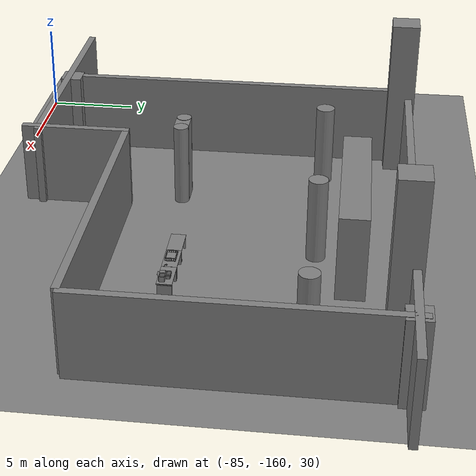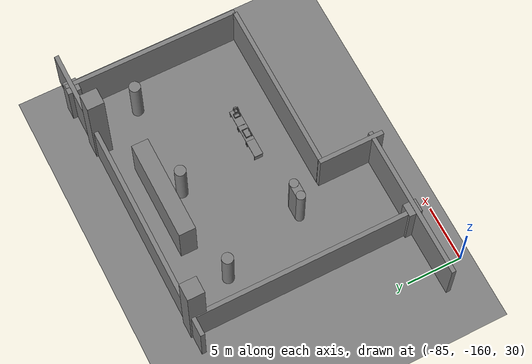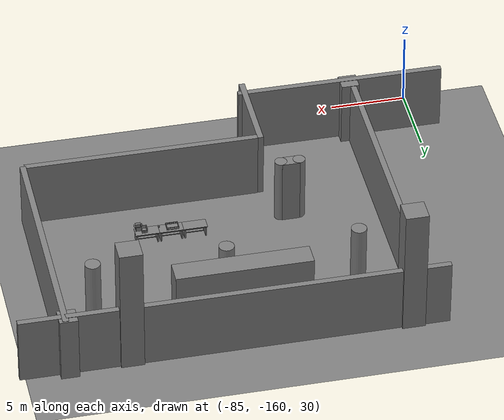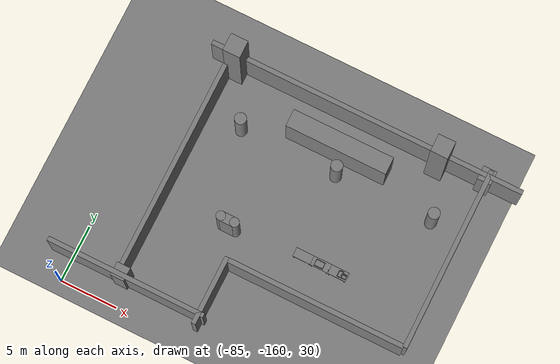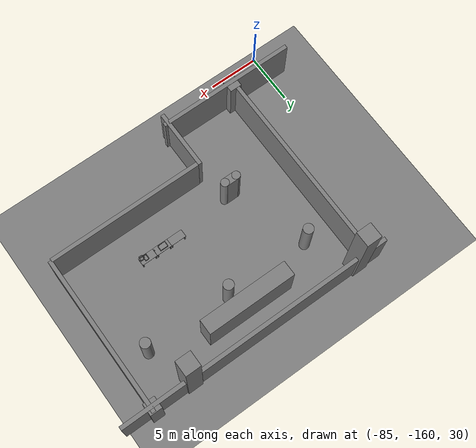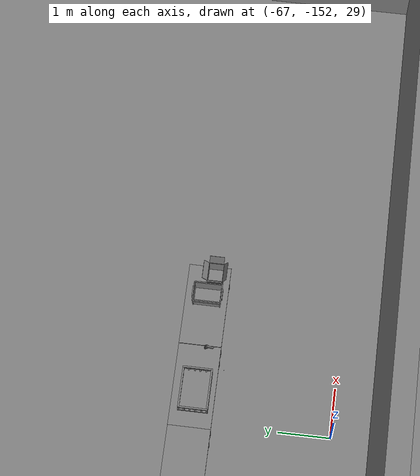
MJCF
<mujoco>
    <option gravity="0.000000000 0.000000000 -9.810000420" timestep="0.0049999999" integrator="implicitfast" density="1.225" viscosity="1.8000001e-05" noslip_iterations="10" iterations="100" sdf_iterations="50">
        <flag multiccd="disable"/>
    </option>
    <size memory="1000M"/>
    <compiler coordinate="local"/>
    <worldbody>
        <light cutoff="30" pos="0 1 1" dir="0 -1 -2"/>
        <light cutoff="30" pos="0 -1 1" dir="0 1 -2"/>
        <body pos="-64.866622925 -149.383972168 30.183746338" euler="89.999984741 89.999946594 0.000000000" name="openloong_gripper_2f85_fix_base_usda_bluebox_01">
            <geom contype="1" conaffinity="1" density="1000" type="box" material="" rgba="0.500000000 0.500000000 0.500000000 1.000000000" solimp="0.899999976 0.949999988 0.001000000" friction="1.000000000 0.005000000 0.000100000" solref="0.020000000 1.000000000" margin="0" condim="3" group="0" pos="0.276580811 0.187225342 0.000068665" quat="0.707106948 0.000077471 0.707106352 0.000077486" size="0.100000001 0.057999998 0.010000000" name="openloong_gripper_2f85_fix_base_usda_geom_BB7E4A3C_963E_4E0D_A4F8_041611DA4FB1"/>
            <geom contype="1" conaffinity="1" density="1000" type="box" material="" rgba="0.500000000 0.500000000 0.500000000 1.000000000" solimp="0.899999976 0.949999988 0.001000000" friction="1.000000000 0.005000000 0.000100000" solref="0.020000000 1.000000000" margin="0" condim="3" group="0" pos="0.000000000 0.002883911 0.000000000" quat="0.999999881 0.000000000 0.000000000 0.000000000" size="0.254000008 0.003000000 0.172000006" name="openloong_gripper_2f85_fix_base_usda_geom_EC15AB10_6E6D_4015_82FA_57C0F08201DB"/>
            <geom contype="1" conaffinity="1" density="1000" type="box" material="" rgba="0.500000000 0.500000000 0.500000000 1.000000000" solimp="0.899999976 0.949999988 0.001000000" friction="1.000000000 0.005000000 0.000100000" solref="0.020000000 1.000000000" margin="0" condim="3" group="0" pos="0.000000000 0.124874115 0.173484802" quat="0.999796331 0.020176515 -0.000000015 0.000000030" size="0.259999990 0.119999997 0.007000000" name="openloong_gripper_2f85_fix_base_usda_geom_D2D0D2AF_6578_489A_8649_2DED257A303F"/>
            <geom contype="1" conaffinity="1" density="1000" type="box" material="" rgba="0.500000000 0.500000000 0.500000000 1.000000000" solimp="0.899999976 0.949999988 0.001000000" friction="1.000000000 0.005000000 0.000100000" solref="0.020000000 1.000000000" margin="0" condim="3" group="0" pos="0.000000000 0.124874115 -0.173469543" quat="0.999796331 -0.020176545 -0.000000015 0.000000000" size="0.259999990 0.119999997 0.007000000" name="openloong_gripper_2f85_fix_base_usda_geom_06772391_AA95_4552_B3DA_E3E3DF75193D"/>
            <geom contype="1" conaffinity="1" density="1000" type="box" material="" rgba="0.500000000 0.500000000 0.500000000 1.000000000" solimp="0.899999976 0.949999988 0.001000000" friction="1.000000000 0.005000000 0.000100000" solref="0.020000000 1.000000000" margin="0" condim="3" group="0" pos="0.000000000 0.214008331 0.188980103" quat="0.999912977 0.013176724 0.000000015 0.000000000" size="0.259999990 0.029999999 0.012500000" name="openloong_gripper_2f85_fix_base_usda_geom_DAD2E8C7_CE5F_406A_99BC_633ECA11B393"/>
            <geom contype="1" conaffinity="1" density="1000" type="box" material="" rgba="0.500000000 0.500000000 0.500000000 1.000000000" solimp="0.899999976 0.949999988 0.001000000" friction="1.000000000 0.005000000 0.000100000" solref="0.020000000 1.000000000" margin="0" condim="3" group="0" pos="-0.258361816 0.125289917 0.001876831" quat="0.702796936 -0.020792112 0.710783124 0.020769298" size="0.189999998 0.119999997 0.009000000" name="openloong_gripper_2f85_fix_base_usda_geom_8C23881C_DB48_461F_BBA6_5F6C9E6EADE2"/>
            <geom contype="1" conaffinity="1" density="1000" type="box" material="" rgba="0.500000000 0.500000000 0.500000000 1.000000000" solimp="0.899999976 0.949999988 0.001000000" friction="1.000000000 0.005000000 0.000100000" solref="0.020000000 1.000000000" margin="0" condim="3" group="0" pos="0.000000000 0.214008331 -0.188980103" quat="0.999912977 -0.013176769 0.000000030 0.000000015" size="0.259999990 0.029999999 0.012500000" name="openloong_gripper_2f85_fix_base_usda_geom_AF01487C_5CA9_4AC0_8AD7_E2B573859FD9"/>
            <geom contype="1" conaffinity="1" density="1000" type="box" material="" rgba="0.500000000 0.500000000 0.500000000 1.000000000" solimp="0.899999976 0.949999988 0.001000000" friction="1.000000000 0.005000000 0.000100000" solref="0.020000000 1.000000000" margin="0" condim="3" group="0" pos="-0.276611328 0.187225342 0.000068665" quat="0.707106650 0.000077441 0.707106709 0.000077456" size="0.100000001 0.057999998 0.010000000" name="openloong_gripper_2f85_fix_base_usda_geom_53A0FF07_2408_4313_BBAA_E1E8FDE7BA07"/>
            <geom contype="1" conaffinity="1" density="1000" type="box" material="" rgba="0.500000000 0.500000000 0.500000000 1.000000000" solimp="0.899999976 0.949999988 0.001000000" friction="1.000000000 0.005000000 0.000100000" solref="0.020000000 1.000000000" margin="0" condim="3" group="0" pos="0.258331299 0.125289917 0.001876831" quat="0.702851415 0.018856421 0.710823774 -0.019329369" size="0.189999998 0.119999997 0.009000000" name="openloong_gripper_2f85_fix_base_usda_geom_8FD8753B_6F6D_434C_9456_8B3B41E86F3D"/>
            <freejoint name="openloong_gripper_2f85_fix_base_usda_bluebox_01_joint"/>
            <site size="0.005000000 0.005000000 0.005000000" rgba="0.500000000 0.500000000 0.500000000 1.000000000" pos="0.000000000 0.000000000 0.000000000" quat="0.999961913 0.008726534 0.000000000 0.000000000" group="0" type="sphere" name="openloong_gripper_2f85_fix_base_usda_bluebox_01site"/>
        </body>
        <body pos="-64.496299744 -149.491867065 30.235729218" euler="0.000000000 0.000000000 89.999946594" name="openloong_gripper_2f85_fix_base_usda_cardboardbox_01">
            <geom contype="1" conaffinity="1" density="1000" type="box" material="" rgba="0.500000000 0.500000000 0.500000000 1.000000000" solimp="0.899999976 0.949999988 0.001000000" friction="1.000000000 0.005000000 0.000100000" solref="0.020000000 1.000000000" margin="0" condim="3" group="0" pos="-0.003166199 -0.004086494 0.005052090" quat="1.000000000 0.000000000 0.000000000 0.000000000" size="0.142499998 0.177500010 0.005000000" name="openloong_gripper_2f85_fix_base_usda_geom_F38D128E_7B1E_4D6C_9670_56643B006C77"/>
            <geom contype="1" conaffinity="1" density="1000" type="box" material="" rgba="0.500000000 0.500000000 0.500000000 1.000000000" solimp="0.899999976 0.949999988 0.001000000" friction="1.000000000 0.005000000 0.000100000" solref="0.020000000 1.000000000" margin="0" condim="3" group="0" pos="-0.003166199 0.170316696 0.150570869" quat="1.000000000 0.000000000 0.000000000 0.000000000" size="0.142499998 0.005000000 0.149999991" name="openloong_gripper_2f85_fix_base_usda_geom_5AFBE849_A323_4D14_95CD_9092206FD01C"/>
            <geom contype="1" conaffinity="1" density="1000" type="box" material="" rgba="0.500000000 0.500000000 0.500000000 1.000000000" solimp="0.899999976 0.949999988 0.001000000" friction="1.000000000 0.005000000 0.000100000" solref="0.020000000 1.000000000" margin="0" condim="3" group="0" pos="-0.147399902 -0.005307198 0.150570869" quat="1.000000000 0.000000000 0.000000000 0.000000000" size="0.005000000 0.177500010 0.149999991" name="openloong_gripper_2f85_fix_base_usda_geom_5D505BB8_91A9_47CC_A536_76F6F709B524"/>
            <geom contype="1" conaffinity="1" density="1000" type="box" material="" rgba="0.500000000 0.500000000 0.500000000 1.000000000" solimp="0.899999976 0.949999988 0.001000000" friction="1.000000000 0.005000000 0.000100000" solref="0.020000000 1.000000000" margin="0" condim="3" group="0" pos="0.140275955 -0.005307198 0.150570869" quat="1.000000000 0.000000000 0.000000000 0.000000000" size="0.005000000 0.177500010 0.149999991" name="openloong_gripper_2f85_fix_base_usda_geom_F53A55CF_1838_4FE1_8742_F0C5DA11C213"/>
            <geom contype="1" conaffinity="1" density="1000" type="box" material="" rgba="0.500000000 0.500000000 0.500000000 1.000000000" solimp="0.899999976 0.949999988 0.001000000" friction="1.000000000 0.005000000 0.000100000" solref="0.020000000 1.000000000" margin="0" condim="3" group="0" pos="-0.003166199 -0.181550980 0.150570869" quat="1.000000000 0.000000000 0.000000000 0.000000000" size="0.142499998 0.005000000 0.149999991" name="openloong_gripper_2f85_fix_base_usda_geom_B88672E6_CFB5_407D_9478_FABD25E71E53"/>
            <freejoint name="openloong_gripper_2f85_fix_base_usda_cardboardbox_01_joint"/>
            <site size="0.005000000 0.005000000 0.005000000" rgba="0.500000000 0.500000000 0.500000000 1.000000000" pos="0.000000000 0.000000000 0.000000000" quat="0.999961913 0.008726535 0.000000000 0.000000000" group="0" type="sphere" name="openloong_gripper_2f85_fix_base_usda_site_1A9C25D1_A998_45EB_BFCB_B48C3FB4D5FF"/>
            <body pos="0.139160156 -0.004048347 0.301930904" euler="-179.999954224 49.383502960 179.999954224" name="openloong_gripper_2f85_fix_base_usda_A1_006">
                <geom contype="1" conaffinity="1" density="1000" type="box" material="" rgba="0.500000000 0.500000000 0.500000000 1.000000000" solimp="0.899999976 0.949999988 0.001000000" friction="1.000000000 0.005000000 0.000100000" solref="0.020000000 1.000000000" margin="0" condim="3" group="0" pos="-0.071587563 0.000009537 0.001745224" quat="0.999999881 0.000000000 0.000000000 0.000000000" size="0.071249999 0.179999992 0.002500000" name="openloong_gripper_2f85_fix_base_usda_geom_68BF6D63_CC62_4444_B7E2_943C1928637D"/>
                <joint armature="0" stiffness="0.07" damping="0.0099999998" axis="0.000000 1.000000 0.000000" type="hinge" name="openloong_gripper_2f85_fix_base_usda_A1_006"/>
            </body>
            <body pos="-0.145902634 -0.004086494 0.301938057" euler="-180.000000000 -60.000011444 -180.000000000" name="openloong_gripper_2f85_fix_base_usda_A2_006">
                <geom contype="1" conaffinity="1" density="1000" type="box" material="" rgba="0.500000000 0.500000000 0.500000000 1.000000000" solimp="0.899999976 0.949999988 0.001000000" friction="1.000000000 0.005000000 0.000100000" solref="0.020000000 1.000000000" margin="0" condim="3" group="0" pos="0.071268082 0.000009537 0.002717972" quat="0.000002921 0.000000000 -0.000000030 0.999999881" size="0.071249999 0.179999992 0.002500000" name="openloong_gripper_2f85_fix_base_usda_geom_80789D4E_E15D_4409_A5B2_FDB0C6FDF9EE"/>
                <joint armature="0" stiffness="0.07" damping="0.0099999998" axis="0.000000 1.000000 0.000000" type="hinge" name="openloong_gripper_2f85_fix_base_usda_A2_006"/>
            </body>
            <body pos="-0.003385544 0.175991058 0.301930904" euler="-125.858116150 -0.000004561 0.000002331" name="openloong_gripper_2f85_fix_base_usda_B2_006">
                <geom contype="1" conaffinity="1" density="1000" type="box" material="" rgba="0.500000000 0.500000000 0.500000000 1.000000000" solimp="0.899999976 0.949999988 0.001000000" friction="1.000000000 0.005000000 0.000100000" solref="0.020000000 1.000000000" margin="0" condim="3" group="0" pos="0.000009537 -0.070939064 -0.002470016" quat="0.999614120 0.027776197 -0.000000015 0.000000030" size="0.137500003 0.064999998 0.005000000" name="openloong_gripper_2f85_fix_base_usda_geom_1DDAEB51_70EA_407D_A440_3EB873E9C909"/>
                <joint armature="0" stiffness="0.07" damping="0.0099999998" axis="1.000000 0.000000 0.000000" type="hinge" name="openloong_gripper_2f85_fix_base_usda_B2_006"/>
            </body>
            <body pos="-0.003385544 -0.184140205 0.301938057" euler="147.805557251 0.000000000 0.000000000" name="openloong_gripper_2f85_fix_base_usda_B1_006">
                <geom contype="1" conaffinity="1" density="1000" type="box" material="" rgba="0.500000000 0.500000000 0.500000000 1.000000000" solimp="0.899999976 0.949999988 0.001000000" friction="1.000000000 0.005000000 0.000100000" solref="0.020000000 1.000000000" margin="0" condim="3" group="0" pos="-0.000028610 0.070202351 -0.002703667" quat="0.999614179 -0.027776167 0.000000000 0.000000000" size="0.137500003 0.064999998 0.005000000" name="openloong_gripper_2f85_fix_base_usda_geom_6314881A_DC8F_4715_889A_CA289F0710DE"/>
                <joint armature="0" stiffness="0.07" damping="0.0099999998" axis="1.000000 0.000000 0.000000" type="hinge" name="openloong_gripper_2f85_fix_base_usda_B1_006"/>
            </body>
        </body>
        <body pos="-65.882858276 -149.481979370 30.229999542" euler="-64.487716675 0.000000000 0.000000000" name="openloong_gripper_2f85_fix_base_usda_Barcode">
            <geom contype="1" conaffinity="1" density="1000" type="box" material="" rgba="0.500000000 0.500000000 0.500000000 1.000000000" solimp="0.899999976 0.949999988 0.001000000" friction="1.000000000 0.005000000 0.000100000" solref="0.020000000 1.000000000" margin="0" condim="3" group="0" pos="0.000000000 0.013038635 0.001419067" quat="0.000000000 0.000000000 0.000000000 1.000000119" size="0.034000002 0.010000000 0.017999999" name="openloong_gripper_2f85_fix_base_usda_geom_E24FA1D8_9FC9_41E8_806F_FBB5138B7D8E"/>
            <geom contype="1" conaffinity="1" density="1000" type="box" material="" rgba="0.500000000 0.500000000 0.500000000 1.000000000" solimp="0.899999976 0.949999988 0.001000000" friction="1.000000000 0.005000000 0.000100000" solref="0.020000000 1.000000000" margin="0" condim="3" group="0" pos="0.000000000 -0.035301208 -0.007095337" quat="0.000000000 0.000000000 -0.043619365 0.999048233" size="0.028999999 0.010000000 0.020000000" name="openloong_gripper_2f85_fix_base_usda_geom_5EBC053F_0333_4AD7_B64B_6C1E91C24869"/>
            <geom contype="1" conaffinity="1" density="1000" type="box" material="" rgba="0.500000000 0.500000000 0.500000000 1.000000000" solimp="0.899999976 0.949999988 0.001000000" friction="1.000000000 0.005000000 0.000100000" solref="0.020000000 1.000000000" margin="0" condim="3" group="0" pos="0.000000000 -0.043411255 -0.011749268" quat="0.922262907 0.386563420 0.000000000 0.000000000" size="0.026000001 0.010000000 0.020000000" name="openloong_gripper_2f85_fix_base_usda_geom_76930C3A_67DF_40DE_AAC9_2A5CEAEFA3CE"/>
            <geom contype="1" conaffinity="1" density="1000" type="box" material="" rgba="0.500000000 0.500000000 0.500000000 1.000000000" solimp="0.899999976 0.949999988 0.001000000" friction="1.000000000 0.005000000 0.000100000" solref="0.020000000 1.000000000" margin="0" condim="3" group="0" pos="0.000000000 -0.016967773 -0.031860352" quat="0.000000000 0.000000000 0.000000000 1.000000119" size="0.008000000 0.010000000 0.013000000" name="openloong_gripper_2f85_fix_base_usda_geom_C1B28C62_1BA0_4D24_9B72_33BE06C2BB52"/>
            <geom contype="1" conaffinity="1" density="1000" type="box" material="" rgba="0.500000000 0.500000000 0.500000000 1.000000000" solimp="0.899999976 0.949999988 0.001000000" friction="1.000000000 0.005000000 0.000100000" solref="0.020000000 1.000000000" margin="0" condim="3" group="0" pos="0.000000000 -0.001869202 0.000312805" quat="0.953716993 0.300705761 0.000000000 0.000000000" size="0.032000002 0.010000000 0.018999999" name="openloong_gripper_2f85_fix_base_usda_geom_CDE2B8E5_9E54_4CD6_AA0B_C5A2C98CAD1B"/>
            <geom contype="1" conaffinity="1" density="1000" type="box" material="" rgba="0.500000000 0.500000000 0.500000000 1.000000000" solimp="0.899999976 0.949999988 0.001000000" friction="1.000000000 0.005000000 0.000100000" solref="0.020000000 1.000000000" margin="0" condim="3" group="0" pos="0.000000000 -0.019531250 -0.003173828" quat="0.953716993 0.300705761 0.000000000 0.000000000" size="0.030999999 0.010000000 0.020000000" name="openloong_gripper_2f85_fix_base_usda_geom_C75023F0_6D6F_4243_92E5_6BBE485C20B8"/>
            <geom contype="1" conaffinity="1" density="1000" type="box" material="" rgba="0.500000000 0.500000000 0.500000000 1.000000000" solimp="0.899999976 0.949999988 0.001000000" friction="1.000000000 0.005000000 0.000100000" solref="0.020000000 1.000000000" margin="0" condim="3" group="0" pos="0.000000000 -0.035301208 -0.007095337" quat="0.953716993 0.300705761 0.000000000 0.000000000" size="0.028999999 0.010000000 0.020000000" name="openloong_gripper_2f85_fix_base_usda_geom_157458EC_3129_4635_88D0_3586540CD472"/>
            <geom contype="1" conaffinity="1" density="1000" type="box" material="" rgba="0.500000000 0.500000000 0.500000000 1.000000000" solimp="0.899999976 0.949999988 0.001000000" friction="1.000000000 0.005000000 0.000100000" solref="0.020000000 1.000000000" margin="0" condim="3" group="0" pos="0.000000000 -0.042617798 -0.071121216" quat="0.000000000 0.000000000 0.000000000 1.000000119" size="0.013000000 0.021000000 0.059999999" name="openloong_gripper_2f85_fix_base_usda_geom_709F0B38_C7C3_4408_B9C1_F36DEABCACCA"/>
            <freejoint name="openloong_gripper_2f85_fix_base_usda_Barcode_joint"/>
            <site size="0.005000000 0.005000000 0.005000000" rgba="0.500000000 0.500000000 0.500000000 1.000000000" pos="0.000000000 0.000000000 0.000000000" quat="1.000000000 0.000000000 0.000000000 0.000000000" group="0" type="sphere" name="openloong_gripper_2f85_fix_base_usda_Barcode_site"/>
        </body>
        <body pos="-66.745018005 -149.392349243 30.184000015" euler="0.000000000 0.000000000 89.999946594" name="[22332675511151]_Basket_01">
            <geom contype="1" conaffinity="1" density="1000" type="box" material="" rgba="0.500000000 0.500000000 0.500000000 1.000000000" solimp="0.899999976 0.949999988 0.001000000" friction="1.000000000 0.005000000 0.000100000" solref="0.020000000 1.000000000" margin="0" condim="3" group="0" pos="-0.052425385 0.389207840 0.089787483" quat="0.707107008 0.000000000 0.000000000 0.707106411" size="0.014249999 0.014249999 0.059999999" name="[22332675511151]_geom_C467BD4B_234A_49AD_B5A9_227F6DFE88B7"/>
            <geom contype="1" conaffinity="1" density="1000" type="box" material="" rgba="0.500000000 0.500000000 0.500000000 1.000000000" solimp="0.899999976 0.949999988 0.001000000" friction="1.000000000 0.005000000 0.000100000" solref="0.020000000 1.000000000" margin="0" condim="3" group="0" pos="0.264015198 -0.133043289 0.089787483" quat="0.707107008 0.000000000 0.000000000 0.707106411" size="0.014249999 0.014249999 0.059999999" name="[22332675511151]_geom_18262C78_FCB8_4023_8552_F098BD0467BF"/>
            <geom contype="1" conaffinity="1" density="1000" type="box" material="" rgba="0.500000000 0.500000000 0.500000000 1.000000000" solimp="0.899999976 0.949999988 0.001000000" friction="1.000000000 0.005000000 0.000100000" solref="0.020000000 1.000000000" margin="0" condim="3" group="0" pos="-0.264015198 -0.265548706 0.089793205" quat="0.707107008 0.000000000 0.000000000 0.707106411" size="0.014249999 0.014249999 0.059999999" name="[22332675511151]_geom_1EDAE207_A354_4339_B99A_8E4E0D00BE02"/>
            <geom contype="1" conaffinity="1" density="1000" type="box" material="" rgba="0.500000000 0.500000000 0.500000000 1.000000000" solimp="0.899999976 0.949999988 0.001000000" friction="1.000000000 0.005000000 0.000100000" solref="0.020000000 1.000000000" margin="0" condim="3" group="0" pos="-0.160263062 -0.389322281 0.089793205" quat="0.707107008 0.000000000 0.000000000 0.707106411" size="0.014249999 0.014249999 0.059999999" name="[22332675511151]_geom_522A7C35_83A0_4AC8_9E8F_CC1AB961984E"/>
            <geom contype="1" conaffinity="1" density="1000" type="box" material="" rgba="0.500000000 0.500000000 0.500000000 1.000000000" solimp="0.899999976 0.949999988 0.001000000" friction="1.000000000 0.005000000 0.000100000" solref="0.020000000 1.000000000" margin="0" condim="3" group="0" pos="0.162265778 -0.389322281 0.089787483" quat="0.707107008 0.000000000 0.000000000 0.707106411" size="0.014249999 0.014249999 0.059999999" name="[22332675511151]_geom_08424331_C31E_4CAB_9602_CD13BB20E133"/>
            <geom contype="1" conaffinity="1" density="1000" type="box" material="" rgba="0.500000000 0.500000000 0.500000000 1.000000000" solimp="0.899999976 0.949999988 0.001000000" friction="1.000000000 0.005000000 0.000100000" solref="0.020000000 1.000000000" margin="0" condim="3" group="0" pos="0.264015198 0.389207840 0.089787483" quat="0.707107008 0.000000000 0.000000000 0.707106411" size="0.014249999 0.014249999 0.059999999" name="[22332675511151]_geom_FBCC5CE9_08CD_4EC1_8818_712CD32038D2"/>
            <geom contype="1" conaffinity="1" density="1000" type="box" material="" rgba="0.500000000 0.500000000 0.500000000 1.000000000" solimp="0.899999976 0.949999988 0.001000000" friction="1.000000000 0.005000000 0.000100000" solref="0.020000000 1.000000000" margin="0" condim="3" group="0" pos="-0.264015198 -0.133043289 0.089793205" quat="0.707107008 0.000000000 0.000000000 0.707106411" size="0.014249999 0.014249999 0.059999999" name="[22332675511151]_geom_9DBF7EE0_ACB7_4EAF_A81F_2D2A10792DFC"/>
            <geom contype="1" conaffinity="1" density="1000" type="box" material="" rgba="0.500000000 0.500000000 0.500000000 1.000000000" solimp="0.899999976 0.949999988 0.001000000" friction="1.000000000 0.005000000 0.000100000" solref="0.020000000 1.000000000" margin="0" condim="3" group="0" pos="-0.264026642 0.269256592 0.089793205" quat="0.707107008 0.000000000 0.000000000 0.707106411" size="0.014249999 0.014249999 0.059999999" name="[22332675511151]_geom_93C8E2C4_F48F_47C7_9A4F_BDFC3963A537"/>
            <geom contype="1" conaffinity="1" density="1000" type="box" material="" rgba="0.500000000 0.500000000 0.500000000 1.000000000" solimp="0.899999976 0.949999988 0.001000000" friction="1.000000000 0.005000000 0.000100000" solref="0.020000000 1.000000000" margin="0" condim="3" group="0" pos="0.054462433 0.389207840 0.089787483" quat="0.707107008 0.000000000 0.000000000 0.707106411" size="0.014249999 0.014249999 0.059999999" name="[22332675511151]_geom_0564A0CD_01EC_4E8F_9E54_4A32FA935AB7"/>
            <geom contype="1" conaffinity="1" density="1000" type="box" material="" rgba="0.500000000 0.500000000 0.500000000 1.000000000" solimp="0.899999976 0.949999988 0.001000000" friction="1.000000000 0.005000000 0.000100000" solref="0.020000000 1.000000000" margin="0" condim="3" group="0" pos="0.054462433 -0.389322281 0.089787483" quat="0.707107008 0.000000000 0.000000000 0.707106411" size="0.014249999 0.014249999 0.059999999" name="[22332675511151]_geom_1B8AC8E8_AF47_40BD_9255_92B30B719E23"/>
            <geom contype="1" conaffinity="1" density="1000" type="box" material="" rgba="0.500000000 0.500000000 0.500000000 1.000000000" solimp="0.899999976 0.949999988 0.001000000" friction="1.000000000 0.005000000 0.000100000" solref="0.020000000 1.000000000" margin="0" condim="3" group="0" pos="0.264015198 0.269256592 0.089793205" quat="0.707107008 0.000000000 0.000000000 0.707106411" size="0.014249999 0.014249999 0.059999999" name="[22332675511151]_geom_1CDBC780_5A23_4597_9FEB_F9FC24F2FEA4"/>
            <geom contype="1" conaffinity="1" density="1000" type="box" material="" rgba="0.500000000 0.500000000 0.500000000 1.000000000" solimp="0.899999976 0.949999988 0.001000000" friction="1.000000000 0.005000000 0.000100000" solref="0.020000000 1.000000000" margin="0" condim="3" group="0" pos="0.264015198 -0.389322281 0.089787483" quat="0.707107008 0.000000000 0.000000000 0.707106411" size="0.014249999 0.014249999 0.059999999" name="[22332675511151]_geom_0AF50342_02EF_4518_8483_384E449E966A"/>
            <geom contype="1" conaffinity="1" density="1000" type="box" material="" rgba="0.500000000 0.500000000 0.500000000 1.000000000" solimp="0.899999976 0.949999988 0.001000000" friction="1.000000000 0.005000000 0.000100000" solref="0.020000000 1.000000000" margin="0" condim="3" group="0" pos="0.000000000 0.000000000 0.015998840" quat="0.707107008 0.000000000 0.000000000 0.707106411" size="0.403499991 0.279000014 0.015750000" name="[22332675511151]_geom_8E70B662_DC25_468B_A84E_35C9BD0128A4"/>
            <geom contype="1" conaffinity="1" density="1000" type="box" material="" rgba="0.500000000 0.500000000 0.500000000 1.000000000" solimp="0.899999976 0.949999988 0.001000000" friction="1.000000000 0.005000000 0.000100000" solref="0.020000000 1.000000000" margin="0" condim="3" group="0" pos="0.000000000 -0.389476776 0.163619041" quat="0.707107008 0.000000000 0.000000000 0.707106411" size="0.015000000 0.277500004 0.015750000" name="[22332675511151]_geom_31090109_4342_4822_B65B_F49C26570702"/>
            <geom contype="1" conaffinity="1" density="1000" type="box" material="" rgba="0.500000000 0.500000000 0.500000000 1.000000000" solimp="0.899999976 0.949999988 0.001000000" friction="1.000000000 0.005000000 0.000100000" solref="0.020000000 1.000000000" margin="0" condim="3" group="0" pos="0.162265778 0.389207840 0.089787483" quat="0.707107008 0.000000000 0.000000000 0.707106411" size="0.014249999 0.014249999 0.059999999" name="[22332675511151]_geom_95062BA2_89C5_4416_BB09_D187D9E9AC12"/>
            <geom contype="1" conaffinity="1" density="1000" type="box" material="" rgba="0.500000000 0.500000000 0.500000000 1.000000000" solimp="0.899999976 0.949999988 0.001000000" friction="1.000000000 0.005000000 0.000100000" solref="0.020000000 1.000000000" margin="0" condim="3" group="0" pos="0.000000000 0.389471054 0.163619041" quat="0.707107008 0.000000000 0.000000000 0.707106411" size="0.015000000 0.277500004 0.015750000" name="[22332675511151]_geom_DE369B98_6213_4CCE_9677_CD21A3D58401"/>
            <geom contype="1" conaffinity="1" density="1000" type="box" material="" rgba="0.500000000 0.500000000 0.500000000 1.000000000" solimp="0.899999976 0.949999988 0.001000000" friction="1.000000000 0.005000000 0.000100000" solref="0.020000000 1.000000000" margin="0" condim="3" group="0" pos="-0.263511658 0.000000000 0.163619041" quat="0.707107008 0.000000000 0.000000000 0.707106411" size="0.403499991 0.015000000 0.015750000" name="[22332675511151]_geom_4449EB59_B37B_454F_A382_12D77D2A0848"/>
            <geom contype="1" conaffinity="1" density="1000" type="box" material="" rgba="0.500000000 0.500000000 0.500000000 1.000000000" solimp="0.899999976 0.949999988 0.001000000" friction="1.000000000 0.005000000 0.000100000" solref="0.020000000 1.000000000" margin="0" condim="3" group="0" pos="-0.264015198 0.141334534 0.089793205" quat="0.707107008 0.000000000 0.000000000 0.707106411" size="0.014249999 0.014249999 0.059999999" name="[22332675511151]_geom_326349E4_B20F_4DCA_BE8B_41C3B364E766"/>
            <geom contype="1" conaffinity="1" density="1000" type="box" material="" rgba="0.500000000 0.500000000 0.500000000 1.000000000" solimp="0.899999976 0.949999988 0.001000000" friction="1.000000000 0.005000000 0.000100000" solref="0.020000000 1.000000000" margin="0" condim="3" group="0" pos="0.264015198 -0.265548706 0.089787483" quat="0.707107008 0.000000000 0.000000000 0.707106411" size="0.014249999 0.014249999 0.059999999" name="[22332675511151]_geom_ACBD9756_1CF3_441C_B33E_51006FC087D5"/>
            <geom contype="1" conaffinity="1" density="1000" type="box" material="" rgba="0.500000000 0.500000000 0.500000000 1.000000000" solimp="0.899999976 0.949999988 0.001000000" friction="1.000000000 0.005000000 0.000100000" solref="0.020000000 1.000000000" margin="0" condim="3" group="0" pos="-0.160263062 0.389207840 0.089787483" quat="0.707107008 0.000000000 0.000000000 0.707106411" size="0.014249999 0.014249999 0.059999999" name="[22332675511151]_geom_2764FE26_C365_4C40_BCFF_A81CCB0AEE22"/>
            <geom contype="1" conaffinity="1" density="1000" type="box" material="" rgba="0.500000000 0.500000000 0.500000000 1.000000000" solimp="0.899999976 0.949999988 0.001000000" friction="1.000000000 0.005000000 0.000100000" solref="0.020000000 1.000000000" margin="0" condim="3" group="0" pos="-0.052425385 -0.389322281 0.089787483" quat="0.707107008 0.000000000 0.000000000 0.707106411" size="0.014249999 0.014249999 0.059999999" name="[22332675511151]_geom_C5B81D71_7BD1_4C2B_BAA2_4DE8FBDC74B7"/>
            <geom contype="1" conaffinity="1" density="1000" type="box" material="" rgba="0.500000000 0.500000000 0.500000000 1.000000000" solimp="0.899999976 0.949999988 0.001000000" friction="1.000000000 0.005000000 0.000100000" solref="0.020000000 1.000000000" margin="0" condim="3" group="0" pos="-0.264026642 -0.389322281 0.089793205" quat="0.707107008 0.000000000 0.000000000 0.707106411" size="0.014249999 0.014249999 0.059999999" name="[22332675511151]_geom_91ACA9CC_8A3D_4015_B52F_4A889D6FE046"/>
            <geom contype="1" conaffinity="1" density="1000" type="box" material="" rgba="0.500000000 0.500000000 0.500000000 1.000000000" solimp="0.899999976 0.949999988 0.001000000" friction="1.000000000 0.005000000 0.000100000" solref="0.020000000 1.000000000" margin="0" condim="3" group="0" pos="0.264015198 0.141334534 0.089787483" quat="0.707107008 0.000000000 0.000000000 0.707106411" size="0.014249999 0.014249999 0.059999999" name="[22332675511151]_geom_C2D4C726_5382_4887_94D4_97ADA99B9C4C"/>
            <geom contype="1" conaffinity="1" density="1000" type="box" material="" rgba="0.500000000 0.500000000 0.500000000 1.000000000" solimp="0.899999976 0.949999988 0.001000000" friction="1.000000000 0.005000000 0.000100000" solref="0.020000000 1.000000000" margin="0" condim="3" group="0" pos="-0.264015198 0.389207840 0.089793205" quat="0.707107008 0.000000000 0.000000000 0.707106411" size="0.014249999 0.014249999 0.059999999" name="[22332675511151]_geom_43112109_8C70_4094_AB1B_097790C20E8C"/>
            <geom contype="1" conaffinity="1" density="1000" type="box" material="" rgba="0.500000000 0.500000000 0.500000000 1.000000000" solimp="0.899999976 0.949999988 0.001000000" friction="1.000000000 0.005000000 0.000100000" solref="0.020000000 1.000000000" margin="0" condim="3" group="0" pos="0.264015198 0.004480362 0.089787483" quat="0.707107008 0.000000000 0.000000000 0.707106411" size="0.014249999 0.014249999 0.059999999" name="[22332675511151]_geom_A139043D_8989_4590_9C24_882970D5AAB6"/>
            <geom contype="1" conaffinity="1" density="1000" type="box" material="" rgba="0.500000000 0.500000000 0.500000000 1.000000000" solimp="0.899999976 0.949999988 0.001000000" friction="1.000000000 0.005000000 0.000100000" solref="0.020000000 1.000000000" margin="0" condim="3" group="0" pos="0.263694763 -0.000011444 0.163619041" quat="0.707107008 0.000000000 0.000000000 0.707106411" size="0.403499991 0.015000000 0.015750000" name="[22332675511151]_geom_FE74A007_44BF_4450_B244_88176DEB68D2"/>
            <geom contype="1" conaffinity="1" density="1000" type="box" material="" rgba="0.500000000 0.500000000 0.500000000 1.000000000" solimp="0.899999976 0.949999988 0.001000000" friction="1.000000000 0.005000000 0.000100000" solref="0.020000000 1.000000000" margin="0" condim="3" group="0" pos="-0.264015198 0.004480362 0.089793205" quat="0.707107008 0.000000000 0.000000000 0.707106411" size="0.014249999 0.014249999 0.059999999" name="[22332675511151]_geom_16019C86_8390_4F23_8F79_330515911499"/>
            <freejoint name="[22332675511151]_joint_4EA77842_E46D_4E0F_AFF9_FCA11EDF9C21"/>
        </body>
        <body pos="0.000000000 0.000000000 0.000000000" euler="0.000000000 0.000000000 0.000000000" name="Static Objects_Static Objects">
            <geom contype="1" conaffinity="1" density="1000" type="box" material="" rgba="0.500000000 0.500000000 0.500000000 1.000000000" solimp="0.899999976 0.949999988 0.001000000" friction="1.000000000 0.005000000 0.000100000" solref="0.020000000 1.000000000" margin="0" condim="3" group="0" pos="-67.544113159 -149.365814209 29.727830887" quat="0.500000417 0.499999970 0.499999553 0.499999970" size="0.381000012 0.319999993 0.041000001" name="Static Objects_geom_DD10E2C6_CC3C_4239_99B9_20912F061595"/>
            <geom contype="1" conaffinity="1" density="1000" type="box" material="" rgba="0.500000000 0.500000000 0.500000000 1.000000000" solimp="0.899999976 0.949999988 0.001000000" friction="1.000000000 0.005000000 0.000100000" solref="0.020000000 1.000000000" margin="0" condim="3" group="0" pos="-68.239501953 -149.365814209 30.086868286" quat="0.500000417 0.499999970 0.499999553 0.499999970" size="0.370999992 0.039500002 0.745000005" name="Static Objects_geom_29494491_A6B8_43A8_87E2_8B3DD376E718"/>
            <geom contype="1" conaffinity="1" density="1000" type="box" material="" rgba="0.500000000 0.500000000 0.500000000 1.000000000" solimp="0.899999976 0.949999988 0.001000000" friction="1.000000000 0.005000000 0.000100000" solref="0.020000000 1.000000000" margin="0" condim="3" group="0" pos="-68.239501953 -149.365814209 30.147235870" quat="0.500000417 0.499999970 0.499999553 0.499999970" size="0.400000006 0.022000000 0.800000012" name="Static Objects_geom_3FF96C2D_8E6F_4F86_A63B_4F56DE91ED5E"/>
            <geom contype="1" conaffinity="1" density="1000" type="box" material="" rgba="0.500000000 0.500000000 0.500000000 1.000000000" solimp="0.899999976 0.949999988 0.001000000" friction="1.000000000 0.005000000 0.000100000" solref="0.020000000 1.000000000" margin="0" condim="3" group="0" pos="-68.934890747 -149.365814209 29.727830887" quat="0.500000417 0.499999970 0.499999553 0.499999970" size="0.381000012 0.319999993 0.041000001" name="Static Objects_geom_EE8B800E_7716_4EBE_B01E_F1029E970C52"/>
            <geom contype="1" conaffinity="1" density="1000" type="box" material="" rgba="0.500000000 0.500000000 0.500000000 1.000000000" solimp="0.899999976 0.949999988 0.001000000" friction="1.000000000 0.005000000 0.000100000" solref="0.020000000 1.000000000" margin="0" condim="3" group="0" pos="-68.239501953 -149.365814209 29.561563492" quat="0.500000417 0.499999970 0.499999553 0.499999970" size="0.020000000 0.022000000 0.660000026" name="Static Objects_geom_07CB1600_FFDC_4A70_AD08_52DB8E807540"/>
            <geom contype="1" conaffinity="1" density="1000" type="box" material="" rgba="0.500000000 0.500000000 0.500000000 1.000000000" solimp="0.899999976 0.949999988 0.001000000" friction="1.000000000 0.005000000 0.000100000" solref="0.020000000 1.000000000" margin="0" condim="3" group="0" pos="-65.945671082 -149.365814209 29.727830887" quat="0.500000417 0.499999970 0.499999553 0.499999970" size="0.381000012 0.319999993 0.041000001" name="Static Objects_geom_09A1078C_6E3F_42AA_B8CD_51F0FED33AE3"/>
            <geom contype="1" conaffinity="1" density="1000" type="box" material="" rgba="0.500000000 0.500000000 0.500000000 1.000000000" solimp="0.899999976 0.949999988 0.001000000" friction="1.000000000 0.005000000 0.000100000" solref="0.020000000 1.000000000" margin="0" condim="3" group="0" pos="-66.641059875 -149.365814209 30.086868286" quat="0.500000417 0.499999970 0.499999553 0.499999970" size="0.370999992 0.039500002 0.745000005" name="Static Objects_geom_6082B1F1_5107_4F52_B279_7E70ABAFDE0B"/>
            <geom contype="1" conaffinity="1" density="1000" type="box" material="" rgba="0.500000000 0.500000000 0.500000000 1.000000000" solimp="0.899999976 0.949999988 0.001000000" friction="1.000000000 0.005000000 0.000100000" solref="0.020000000 1.000000000" margin="0" condim="3" group="0" pos="-66.641059875 -149.365814209 30.147235870" quat="0.500000417 0.499999970 0.499999553 0.499999970" size="0.400000006 0.022000000 0.800000012" name="Static Objects_geom_5962F424_81BC_4F3C_B9E2_895EEE5ACA03"/>
            <geom contype="1" conaffinity="1" density="1000" type="box" material="" rgba="0.500000000 0.500000000 0.500000000 1.000000000" solimp="0.899999976 0.949999988 0.001000000" friction="1.000000000 0.005000000 0.000100000" solref="0.020000000 1.000000000" margin="0" condim="3" group="0" pos="-67.336448669 -149.365814209 29.727830887" quat="0.500000417 0.499999970 0.499999553 0.499999970" size="0.381000012 0.319999993 0.041000001" name="Static Objects_geom_C6D45C99_2398_48DA_ACC1_53F138525D84"/>
            <geom contype="1" conaffinity="1" density="1000" type="box" material="" rgba="0.500000000 0.500000000 0.500000000 1.000000000" solimp="0.899999976 0.949999988 0.001000000" friction="1.000000000 0.005000000 0.000100000" solref="0.020000000 1.000000000" margin="0" condim="3" group="0" pos="-66.641059875 -149.365814209 29.561563492" quat="0.500000417 0.499999970 0.499999553 0.499999970" size="0.020000000 0.022000000 0.660000026" name="Static Objects_geom_FC39FCCA_AFB1_48DD_96BA_B2C65693FE96"/>
            <geom contype="1" conaffinity="1" density="1000" type="box" material="" rgba="0.500000000 0.500000000 0.500000000 1.000000000" solimp="0.899999976 0.949999988 0.001000000" friction="1.000000000 0.005000000 0.000100000" solref="0.020000000 1.000000000" margin="0" condim="3" group="0" pos="-64.338577271 -149.365814209 29.727830887" quat="0.500000417 0.499999970 0.499999553 0.499999970" size="0.381000012 0.319999993 0.041000001" name="Static Objects_geom_D7C96DBB_EB38_4AF9_80A3_CF88615E6532"/>
            <geom contype="1" conaffinity="1" density="1000" type="box" material="" rgba="0.500000000 0.500000000 0.500000000 1.000000000" solimp="0.899999976 0.949999988 0.001000000" friction="1.000000000 0.005000000 0.000100000" solref="0.020000000 1.000000000" margin="0" condim="3" group="0" pos="-65.033966064 -149.365814209 30.086868286" quat="0.500000417 0.499999970 0.499999553 0.499999970" size="0.370999992 0.039500002 0.745000005" name="Static Objects_geom_DFBF1BB8_305D_4406_A5ED_799FC4F8A8EB"/>
            <geom contype="1" conaffinity="1" density="1000" type="box" material="" rgba="0.500000000 0.500000000 0.500000000 1.000000000" solimp="0.899999976 0.949999988 0.001000000" friction="1.000000000 0.005000000 0.000100000" solref="0.020000000 1.000000000" margin="0" condim="3" group="0" pos="-65.033966064 -149.365814209 30.147235870" quat="0.500000417 0.499999970 0.499999553 0.499999970" size="0.400000006 0.022000000 0.800000012" name="Static Objects_geom_833A70AB_F754_4C5C_9C97_61A1780B6C25"/>
            <geom contype="1" conaffinity="1" density="1000" type="box" material="" rgba="0.500000000 0.500000000 0.500000000 1.000000000" solimp="0.899999976 0.949999988 0.001000000" friction="1.000000000 0.005000000 0.000100000" solref="0.020000000 1.000000000" margin="0" condim="3" group="0" pos="-65.729354858 -149.365814209 29.727830887" quat="0.500000417 0.499999970 0.499999553 0.499999970" size="0.381000012 0.319999993 0.041000001" name="Static Objects_geom_8998926E_8160_4158_B003_F433BCAC14A7"/>
            <geom contype="1" conaffinity="1" density="1000" type="box" material="" rgba="0.500000000 0.500000000 0.500000000 1.000000000" solimp="0.899999976 0.949999988 0.001000000" friction="1.000000000 0.005000000 0.000100000" solref="0.020000000 1.000000000" margin="0" condim="3" group="0" pos="-65.033966064 -149.365814209 29.561563492" quat="0.500000417 0.499999970 0.499999553 0.499999970" size="0.020000000 0.022000000 0.660000026" name="Static Objects_geom_7EAAEA80_D038_4F25_98ED_17DC83C6A215"/>
            <geom contype="1" conaffinity="1" density="1000" type="box" material="" rgba="0.500000000 0.500000000 0.500000000 1.000000000" solimp="0.899999976 0.949999988 0.001000000" friction="1.000000000 0.005000000 0.000100000" solref="0.020000000 1.000000000" margin="0" condim="3" group="0" pos="-61.754566193 -137.853729248 33.906845093" quat="0.707107067 0.000000000 0.000000000 0.707106471" size="0.759999990 0.759999990 4.500000000" name="Static Objects_geom_8B390FC1_BD6F_4FB9_95A3_7C97866A0FC8"/>
            <geom contype="1" conaffinity="1" density="1000" type="box" material="" rgba="0.500000000 0.500000000 0.500000000 1.000000000" solimp="0.899999976 0.949999988 0.001000000" friction="1.000000000 0.005000000 0.000100000" solref="0.020000000 1.000000000" margin="0" condim="3" group="0" pos="-57.511135101 -144.927108765 31.707921982" quat="1.000000000 0.000000000 0.000000000 0.000000000" size="0.200000003 8.000000000 2.299999952" name="Static Objects_geom_026AD892_5437_480E_BF3F_A187A52181A4"/>
            <geom contype="1" conaffinity="1" density="1000" type="box" material="" rgba="0.500000000 0.500000000 0.500000000 1.000000000" solimp="0.899999976 0.949999988 0.001000000" friction="1.000000000 0.005000000 0.000100000" solref="0.020000000 1.000000000" margin="0" condim="3" group="0" pos="-80.517646790 -157.574050903 31.688196182" quat="0.707107067 0.000000000 0.000000000 0.707106471" size="0.600000024 0.600000024 2.299999952" name="Static Objects_geom_31DB47DA_B64E_496B_A64E_E72204A6532E"/>
            <geom contype="1" conaffinity="1" density="1000" type="box" material="" rgba="0.500000000 0.500000000 0.500000000 1.000000000" solimp="0.899999976 0.949999988 0.001000000" friction="1.000000000 0.005000000 0.000100000" solref="0.020000000 1.000000000" margin="0" condim="3" group="0" pos="-80.711044312 -147.414932251 31.666158676" quat="1.000000000 0.000000000 0.000000000 0.000000000" size="0.200000003 10.000000000 2.299999952" name="Static Objects_geom_5C9729D1_7C82_4A32_A416_A02E8208CFDC"/>
            <geom contype="1" conaffinity="1" density="1000" type="box" material="" rgba="0.500000000 0.500000000 0.500000000 1.000000000" solimp="0.899999976 0.949999988 0.001000000" friction="1.000000000 0.005000000 0.000100000" solref="0.020000000 1.000000000" margin="0" condim="3" group="0" pos="-57.687217712 -137.434692383 31.688196182" quat="0.707107067 0.000000000 0.000000000 0.707106471" size="0.600000024 0.600000024 2.299999952" name="Static Objects_geom_7965EEAF_8602_4230_A5FC_C771E87A3389"/>
            <geom contype="1" conaffinity="1" density="1000" type="box" material="" rgba="0.500000000 0.500000000 0.500000000 1.000000000" solimp="0.899999976 0.949999988 0.001000000" friction="1.000000000 0.005000000 0.000100000" solref="0.020000000 1.000000000" margin="0" condim="3" group="0" pos="-69.537033081 -140.263229370 31.714921951" quat="0.707107067 0.000000000 0.000000000 0.707106471" size="0.759999990 4.500000000 2.299999952" name="Static Objects_geom_9CB1B533_8460_4C27_A4AE_5C3596A79DCE"/>
            <geom contype="1" conaffinity="1" density="1000" type="box" material="" rgba="0.500000000 0.500000000 0.500000000 1.000000000" solimp="0.899999976 0.949999988 0.001000000" friction="1.000000000 0.005000000 0.000100000" solref="0.020000000 1.000000000" margin="0" condim="3" group="0" pos="-80.073638916 -137.853713989 33.906845093" quat="0.707107067 0.000000000 0.000000000 0.707106471" size="0.759999990 0.759999990 4.500000000" name="Static Objects_geom_0F28EB3A_9E9B_420C_91EA_9B3B0958CC75"/>
            <geom contype="1" conaffinity="1" density="1000" type="box" material="" rgba="0.500000000 0.500000000 0.500000000 1.000000000" solimp="0.899999976 0.949999988 0.001000000" friction="1.000000000 0.005000000 0.000100000" solref="0.020000000 1.000000000" margin="0" condim="3" group="0" pos="-73.406707764 -155.734664917 31.707921982" quat="1.000000000 0.000000000 0.000000000 0.000000000" size="0.200000003 3.000000000 2.299999952" name="Static Objects_geom_5BDB44EC_7253_4FC9_90F8_95A63D4E8CDA"/>
            <geom contype="1" conaffinity="1" density="1000" type="box" material="" rgba="0.500000000 0.500000000 0.500000000 1.000000000" solimp="0.899999976 0.949999988 0.001000000" friction="1.000000000 0.005000000 0.000100000" solref="0.020000000 1.000000000" margin="0" condim="3" group="0" pos="-68.497543335 -137.448257446 31.707921982" quat="0.707107067 0.000000000 0.000000000 0.707106471" size="0.200000003 14.000000000 2.299999952" name="Static Objects_geom_BB282222_44C5_4217_A048_294F46F3A49D"/>
            <geom contype="1" conaffinity="1" density="1000" type="cylinder" material="" rgba="0.500000000 0.500000000 0.500000000 1.000000000" solimp="0.899999976 0.949999988 0.001000000" friction="1.000000000 0.005000000 0.000100000" solref="0.020000000 1.000000000" margin="0" condim="3" group="0" pos="-68.868522644 -142.134506226 31.711090088" quat="0.707107067 0.000000000 0.000000000 0.707106471" size="0.509999990 2.299999952 1.000000000" name="Static Objects_geom_8C309066_D66E_4C00_8DA6_723089830D91"/>
            <geom contype="1" conaffinity="1" density="1000" type="plane" material="" rgba="0.500000000 0.500000000 0.500000000 1.000000000" solimp="0.899999976 0.949999988 0.001000000" friction="1.000000000 0.005000000 0.000100000" solref="0.020000000 1.000000000" margin="0" condim="3" group="0" pos="-72.873703003 -147.131927490 29.409669876" quat="1.000000000 0.000000000 0.000000000 0.000000000" size="18.000000000 14.000000000 1.000000000" name="Static Objects_geom_F858407B_7998_4BFD_A6B5_34197C21AB08"/>
            <geom contype="1" conaffinity="1" density="1000" type="box" material="" rgba="0.500000000 0.500000000 0.500000000 1.000000000" solimp="0.899999976 0.949999988 0.001000000" friction="1.000000000 0.005000000 0.000100000" solref="0.020000000 1.000000000" margin="0" condim="3" group="0" pos="-79.943580627 -157.782272339 31.707921982" quat="0.707107067 0.000000000 0.000000000 0.707106471" size="0.200000003 7.000000000 2.299999952" name="Static Objects_geom_9EC95580_3DEF_4338_ABD4_6F3DC3534E57"/>
            <geom contype="1" conaffinity="1" density="1000" type="box" material="" rgba="0.500000000 0.500000000 0.500000000 1.000000000" solimp="0.899999976 0.949999988 0.001000000" friction="1.000000000 0.005000000 0.000100000" solref="0.020000000 1.000000000" margin="0" condim="3" group="0" pos="-65.421028137 -152.903442383 31.707921982" quat="0.707107067 0.000000000 0.000000000 0.707106471" size="0.200000003 7.800000191 2.299999952" name="Static Objects_geom_69CCCAFA_2023_4C4D_ADEC_8B85459A6D51"/>
            <geom contype="1" conaffinity="1" density="1000" type="box" material="" rgba="0.500000000 0.500000000 0.500000000 1.000000000" solimp="0.899999976 0.949999988 0.001000000" friction="1.000000000 0.005000000 0.000100000" solref="0.020000000 1.000000000" margin="0" condim="3" group="0" pos="-74.776908875 -149.964416504 31.688196182" quat="1.000000000 0.000000000 0.000000000 0.000000000" size="0.600000024 0.409999996 2.299999952" name="Static Objects_geom_0F1FFE21_2C0F_45C0_8D97_6E71DDC28017"/>
            <geom contype="1" conaffinity="1" density="1000" type="cylinder" material="" rgba="0.500000000 0.500000000 0.500000000 1.000000000" solimp="0.899999976 0.949999988 0.001000000" friction="1.000000000 0.005000000 0.000100000" solref="0.020000000 1.000000000" margin="0" condim="3" group="0" pos="-60.161884308 -142.134506226 31.711090088" quat="0.707107067 0.000000000 0.000000000 0.707106471" size="0.509999990 2.299999952 1.000000000" name="Static Objects_geom_17525B5A_A247_4FCA_B3F2_4F7FA02F8E1E"/>
            <geom contype="1" conaffinity="1" density="1000" type="cylinder" material="" rgba="0.500000000 0.500000000 0.500000000 1.000000000" solimp="0.899999976 0.949999988 0.001000000" friction="1.000000000 0.005000000 0.000100000" solref="0.020000000 1.000000000" margin="0" condim="3" group="0" pos="-75.382453918 -149.963455200 31.711090088" quat="0.707107067 0.000000000 0.000000000 0.707106471" size="0.409999996 2.299999952 1.000000000" name="Static Objects_geom_E229AEBC_CB9F_410C_B9E8_482A5ABFD88F"/>
            <geom contype="1" conaffinity="1" density="1000" type="cylinder" material="" rgba="0.500000000 0.500000000 0.500000000 1.000000000" solimp="0.899999976 0.949999988 0.001000000" friction="1.000000000 0.005000000 0.000100000" solref="0.020000000 1.000000000" margin="0" condim="3" group="0" pos="-74.154960632 -149.963455200 31.711090088" quat="0.707107067 0.000000000 0.000000000 0.707106471" size="0.409999996 2.299999952 1.000000000" name="Static Objects_geom_D511B674_EC06_419C_B5B8_67BB819BBD5C"/>
            <geom contype="1" conaffinity="1" density="1000" type="cylinder" material="" rgba="0.500000000 0.500000000 0.500000000 1.000000000" solimp="0.899999976 0.949999988 0.001000000" friction="1.000000000 0.005000000 0.000100000" solref="0.020000000 1.000000000" margin="0" condim="3" group="0" pos="-77.566612244 -142.134506226 31.711090088" quat="0.707107067 0.000000000 0.000000000 0.707106471" size="0.509999990 2.299999952 1.000000000" name="Static Objects_geom_A8C72C28_3E34_487B_8D75_700E2D32C5B4"/>
        </body>
        <body pos="-66.291030884 -149.869689941 29.018842697" euler="0.000000000 0.000000000 89.999946594" mocap="true" name="openloong_gripper_2f85_fix_base_usda_leftHandMocap"/>
        <body pos="-66.291030884 -149.869689941 29.018842697" euler="0.000000000 0.000000000 89.999946594" mocap="true" name="openloong_gripper_2f85_fix_base_usda_rightHandMocap"/>
        <body pos="-66.291030884 -149.869689941 30.218843460" euler="0.000000000 0.000000000 89.999946594" name="openloong_gripper_2f85_fix_base_usda_base_link">
            <geom contype="1" conaffinity="1" density="1000" type="mesh" material="" rgba="0.783999979 0.783999979 0.783999979 1.000000000" solimp="0.899999976 0.949999988 0.001000000" friction="1.000000000 0.005000000 0.000100000" solref="0.020000000 1.000000000" margin="0" condim="3" group="3" mesh="base_link" pos="0.000000000 0.000000000 0.000000000" quat="1.000000000 0.000000000 0.000000000 0.000000000" size="1.000000000 1.000000000 1.000000000" name="openloong_gripper_2f85_fix_base_usda__geom_7_C3A12E7D_9889_4AD3_8DE5_C986A257821F"/>
            <site size="0.005000000 0.005000000 0.005000000" rgba="0.500000000 0.500000000 0.500000000 1.000000000" pos="0.000000000 0.000000000 0.000000000" quat="1.000000000 0.000000000 0.000000000 0.000000000" group="0" type="sphere" name="openloong_gripper_2f85_fix_base_usda_imu"/>
            <inertial mass="22.447001" pos="-0.005664100 -0.001336700 0.238289997" diaginertia="0.374352545 0.277180195 0.220617250" quat="0.999247074 0.035235517 -0.015086859 0.006023135"/>
            <body pos="0.000000000 0.000000000 0.299997330" euler="0.000000000 0.000000000 0.000000000" name="openloong_gripper_2f85_fix_base_usda_dummy_body">
                <geom contype="1" conaffinity="1" density="1000" type="sphere" material="" rgba="0.783999979 0.783999979 0.783999979 1.000000000" solimp="0.899999976 0.949999988 0.001000000" friction="1.000000000 0.005000000 0.000100000" solref="0.020000000 1.000000000" margin="0" condim="3" group="3" pos="0.000000000 0.000000000 0.000000000" quat="1.000000000 0.000000000 0.000000000 0.000000000" size="0.010000000 0.000000000 0.000000000" name="openloong_gripper_2f85_fix_base_usda__geom_8_E980C670_6E33_4DB2_B402_9BDD1EE0ABC6"/>
                <joint armature="0.0099999998" stiffness="0" damping="0.1" axis="0.000000 0.000000 1.000000" type="hinge" name="openloong_gripper_2f85_fix_base_usda_dummy_joint"/>
                <site size="0.010000000 0.005000000 0.005000000" rgba="0.500000000 0.500000000 0.500000000 1.000000000" pos="0.000000000 0.000000000 0.000000000" quat="1.000000000 0.000000000 0.000000000 0.000000000" group="3" type="sphere" name="openloong_gripper_2f85_fix_base_usda_dummy_site"/>
            </body>
            <body pos="0.009002686 0.000000000 0.406400681" euler="0.000000000 0.000000000 0.000000000" name="openloong_gripper_2f85_fix_base_usda_Link_head_yaw">
                <geom contype="1" conaffinity="1" density="1000" type="mesh" material="" rgba="0.783999979 0.783999979 0.783999979 1.000000000" solimp="0.899999976 0.949999988 0.001000000" friction="1.000000000 0.005000000 0.000100000" solref="0.020000000 1.000000000" margin="0" condim="3" group="3" mesh="Link_head_yaw" pos="0.000000000 0.000000000 0.000000000" quat="1.000000000 0.000000000 0.000000000 0.000000000" size="1.000000000 1.000000000 1.000000000" name="openloong_gripper_2f85_fix_base_usda__geom_10_7C5D3A47_B664_473E_BB59_443F2B56141F"/>
                <inertial mass="0.84249002" pos="0.000000000 -0.002081400 0.044801001" diaginertia="0.000700588 0.000629000 0.000553812" quat="0.706933022 -0.015675601 0.015677100 0.706933022"/>
                <body pos="0.000000000 -0.034599304 0.048500061" euler="0.000000000 0.000000000 0.000000000" name="openloong_gripper_2f85_fix_base_usda_Link_head_pitch">
                    <geom contype="1" conaffinity="1" density="1000" type="mesh" material="" rgba="0.783999979 0.783999979 0.783999979 1.000000000" solimp="0.899999976 0.949999988 0.001000000" friction="1.000000000 0.005000000 0.000100000" solref="0.020000000 1.000000000" margin="0" condim="3" group="3" mesh="Link_head_pitch" pos="0.000000000 0.000000000 0.000000000" quat="1.000000000 0.000000000 0.000000000 0.000000000" size="1.000000000 1.000000000 1.000000000" name="openloong_gripper_2f85_fix_base_usda__geom_12_C97C0FBB_570A_495D_8609_4106CF04AB98"/>
                    <inertial mass="1.3943" pos="0.020569000 0.033004001 0.125000000" diaginertia="0.006381400 0.006289940 0.004481460" quat="0.973390222 0.008406822 0.228157058 0.019624906"/>
                    <body pos="0.000000000 0.029998779 0.000000000" euler="0.000000000 0.000000000 0.000000000" name="openloong_gripper_2f85_fix_base_usda_neck_center_body">
                        <site size="0.010000000 0.005000000 0.005000000" rgba="0.500000000 0.500000000 0.500000000 1.000000000" pos="0.000000000 0.000000000 0.000000000" quat="1.000000000 0.000000000 0.000000000 0.000000000" group="3" type="sphere" name="openloong_gripper_2f85_fix_base_usda_neck_center_site"/>
                        <body pos="0.020004272 0.000000000 0.149999619" euler="-0.000002229 39.998176575 -90.000205994" name="openloong_gripper_2f85_fix_base_usda_camera_head">
                            <site size="0.010000000 0.005000000 0.005000000" rgba="0.500000000 0.500000000 0.500000000 1.000000000" pos="0.000000000 0.000000000 0.000000000" quat="1.000000000 0.000000000 0.000000000 0.000000000" group="3" type="sphere" name="openloong_gripper_2f85_fix_base_usda_camera_head_site"/>
                        </body>
                    </body>
                </body>
            </body>
            <body pos="0.003997803 -0.161598206 0.392200470" euler="0.000000000 0.000000000 0.000000000" name="openloong_gripper_2f85_fix_base_usda_Link_arm_r_01">
                <geom contype="1" conaffinity="1" density="1000" type="mesh" material="" rgba="0.783999979 0.783999979 0.783999979 1.000000000" solimp="0.899999976 0.949999988 0.001000000" friction="1.000000000 0.005000000 0.000100000" solref="0.020000000 1.000000000" margin="0" condim="3" group="3" mesh="Link_arm_r_01" pos="0.000000000 0.000000000 0.000000000" quat="1.000000000 0.000000000 0.000000000 0.000000000" size="1.000000000 1.000000000 1.000000000" name="openloong_gripper_2f85_fix_base_usda__geom_14_F1E8D318_95DA_4D88_B267_7FA790408997"/>
                <joint armature="0.0099999998" stiffness="0" damping="1" axis="0.000000 -1.000000 0.000000" limited="true" range="-170.000015259 170.000015259" type="hinge" name="openloong_gripper_2f85_fix_base_usda_J_arm_r_01"/>
                <inertial mass="0.75641" pos="0.004494600 -0.038293999 -0.000001874" diaginertia="0.000842990 0.000803050 0.000587120" quat="-0.000163502 0.707098067 0.000812463 0.707115054"/>
                <body pos="-0.041992188 -0.041000366 0.000000000" euler="0.000000000 0.000000000 0.000000000" name="openloong_gripper_2f85_fix_base_usda_Link_arm_r_02">
                    <geom contype="1" conaffinity="1" density="1000" type="mesh" material="" rgba="0.783999979 0.783999979 0.783999979 1.000000000" solimp="0.899999976 0.949999988 0.001000000" friction="1.000000000 0.005000000 0.000100000" solref="0.020000000 1.000000000" margin="0" condim="3" group="3" mesh="Link_arm_r_02" pos="0.000000000 0.000000000 0.000000000" quat="1.000000000 0.000000000 0.000000000 0.000000000" size="1.000000000 1.000000000 1.000000000" name="openloong_gripper_2f85_fix_base_usda__geom_16_B663BBA4_C80B_4449_9509_A0B8CC4FE933"/>
                    <joint armature="0.0099999998" stiffness="0" damping="1" axis="-1.000000 0.000000 0.000000" limited="true" range="-105.000244141 105.000244141" type="hinge" name="openloong_gripper_2f85_fix_base_usda_J_arm_r_02"/>
                    <inertial mass="0.98500001" pos="0.041999999 -0.067430697 0.000000000" diaginertia="0.002262690 0.001730990 0.001154020" quat="0.500000000 0.500000000 -0.500000000 0.500000000"/>
                    <body pos="0.041992188 -0.122596741 0.000000000" euler="0.000000000 0.000000000 0.000000000" name="openloong_gripper_2f85_fix_base_usda_Link_arm_r_03">
                        <geom contype="1" conaffinity="1" density="1000" type="mesh" material="" rgba="0.783999979 0.783999979 0.783999979 1.000000000" solimp="0.899999976 0.949999988 0.001000000" friction="1.000000000 0.005000000 0.000100000" solref="0.020000000 1.000000000" margin="0" condim="3" group="3" mesh="Link_arm_r_03" pos="0.000000000 0.000000000 0.000000000" quat="1.000000000 0.000000000 0.000000000 0.000000000" size="1.000000000 1.000000000 1.000000000" name="openloong_gripper_2f85_fix_base_usda__geom_18_D0AC5B68_BDB7_4DEB_84B3_5D56EAF4338A"/>
                        <joint armature="0.0099999998" stiffness="0" damping="1" axis="0.000000 -1.000000 0.000000" limited="true" range="-170.000015259 170.000015259" type="hinge" name="openloong_gripper_2f85_fix_base_usda_J_arm_r_03"/>
                        <inertial mass="0.95899999" pos="-0.001413580 -0.164663002 0.020757901" diaginertia="0.002101340 0.002064590 0.000754802" quat="0.560480952 0.454391927 -0.443732947 0.531497955"/>
                        <body pos="0.035293579 -0.177406311 0.023998260" euler="0.000000000 0.000000000 0.000000000" name="openloong_gripper_2f85_fix_base_usda_Link_arm_r_04">
                            <geom contype="1" conaffinity="1" density="1000" type="mesh" material="" rgba="0.783999979 0.783999979 0.783999979 1.000000000" solimp="0.899999976 0.949999988 0.001000000" friction="1.000000000 0.005000000 0.000100000" solref="0.020000000 1.000000000" margin="0" condim="3" group="3" mesh="Link_arm_r_04" pos="0.000000000 0.000000000 0.000000000" quat="1.000000000 0.000000000 0.000000000 0.000000000" size="1.000000000 1.000000000 1.000000000" name="openloong_gripper_2f85_fix_base_usda__geom_20_8B86BEF2_20AC_4BCD_A208_47B12BB4A204"/>
                            <joint armature="0.0099999998" stiffness="0" damping="1" axis="-1.000000 0.000000 0.000000" limited="true" range="0.000000000 170.000015259" type="hinge" name="openloong_gripper_2f85_fix_base_usda_J_arm_r_04"/>
                            <inertial mass="0.60000002" pos="-0.038727000 -0.060766999 -0.021003000" diaginertia="0.001092610 0.000712422 0.000645102" quat="0.327701002 0.632602990 -0.467366993 0.523443997"/>
                            <body pos="-0.035293579 -0.103492737 -0.023998260" euler="0.000000000 0.000000000 0.000000000" name="openloong_gripper_2f85_fix_base_usda_Link_arm_r_05">
                                <geom contype="1" conaffinity="1" density="1000" type="mesh" material="" rgba="0.783999979 0.783999979 0.783999979 1.000000000" solimp="0.899999976 0.949999988 0.001000000" friction="1.000000000 0.005000000 0.000100000" solref="0.020000000 1.000000000" margin="0" condim="3" group="3" mesh="Link_arm_r_05" pos="0.000000000 0.000000000 0.000000000" quat="1.000000000 0.000000000 0.000000000 0.000000000" size="1.000000000 1.000000000 1.000000000" name="openloong_gripper_2f85_fix_base_usda__geom_22_2EC99C9D_0BB3_4C3C_BA7E_B6D6798520AA"/>
                                <joint armature="0.0099999998" stiffness="0" damping="1" axis="0.000000 -1.000000 0.000000" limited="true" range="-170.000015259 170.000015259" type="hinge" name="openloong_gripper_2f85_fix_base_usda_J_arm_r_05"/>
                                <inertial mass="0.68976003" pos="0.000032712 -0.068658002 -0.000111780" diaginertia="0.002522510 0.002411100 0.000448695" quat="0.707660973 0.706543028 -0.002603360 0.002470550"/>
                                <body pos="-0.026489258 -0.196502686 0.000000000" euler="0.000000000 0.000000000 0.000000000" name="openloong_gripper_2f85_fix_base_usda_Link_arm_r_06">
                                    <geom contype="1" conaffinity="1" density="1000" type="mesh" material="" rgba="0.783999979 0.783999979 0.783999979 1.000000000" solimp="0.899999976 0.949999988 0.001000000" friction="1.000000000 0.005000000 0.000100000" solref="0.020000000 1.000000000" margin="0" condim="3" group="3" mesh="Link_arm_r_06" pos="0.000000000 0.000000000 0.000000000" quat="1.000000000 0.000000000 0.000000000 0.000000000" size="1.000000000 1.000000000 1.000000000" name="openloong_gripper_2f85_fix_base_usda__geom_24_192AAA9A_965D_4D2C_9248_276C61325BDD"/>
                                    <joint armature="0.0099999998" stiffness="0" damping="1" axis="1.000000 0.000000 0.000000" limited="true" range="-105.000244141 105.000244141" type="hinge" name="openloong_gripper_2f85_fix_base_usda_J_arm_r_06"/>
                                    <inertial mass="0.28" pos="0.026078001 -0.000000896 0.001663700" diaginertia="0.000156930 0.000145601 0.000104979" quat="0.707080841 0.001851080 0.001883810 0.707127810"/>
                                    <body pos="0.026489258 0.000000000 0.031799316" euler="0.000000000 0.000000000 0.000000000" name="openloong_gripper_2f85_fix_base_usda_Link_arm_r_07">
                                        <geom contype="1" conaffinity="1" density="1000" type="mesh" material="" rgba="0.783999979 0.783999979 0.783999979 1.000000000" solimp="0.899999976 0.949999988 0.001000000" friction="1.000000000 0.005000000 0.000100000" solref="0.020000000 1.000000000" margin="0" condim="3" group="3" mesh="Link_arm_r_07" pos="0.000000000 0.000000000 0.000000000" quat="1.000000000 0.000000000 0.000000000 0.000000000" size="1.000000000 1.000000000 1.000000000" name="openloong_gripper_2f85_fix_base_usda__geom_26_E1C1B6E4_373D_4210_9D02_043FFDD39B67"/>
                                        <joint armature="0.0099999998" stiffness="0" damping="1" axis="0.000000 0.000000 1.000000" limited="true" range="-60.000133514 60.000133514" type="hinge" name="openloong_gripper_2f85_fix_base_usda_J_arm_r_07"/>
                                        <inertial mass="0.61353999" pos="-0.007859000 -0.158170000 -0.027736001" diaginertia="0.003037610 0.002570910 0.000729379" quat="0.427542925 0.443532884 -0.553093910 0.560867906"/>
                                        <body pos="0.000000000 0.286994934 -0.270000458" euler="150.000350952 -0.000001649 -0.000000442" name="openloong_gripper_2f85_fix_base_usda_camera_wrist_r">
                                            <site size="0.010000000 0.005000000 0.005000000" rgba="0.500000000 0.500000000 0.500000000 1.000000000" pos="0.000000000 0.000000000 0.000000000" quat="1.000000000 0.000000000 0.000000000 0.000000000" group="3" type="sphere" name="openloong_gripper_2f85_fix_base_usda_camera_wrist_r_site"/>
                                        </body>
                                        <body pos="0.000000000 -0.220008850 -0.033002853" euler="0.000000000 0.000000000 179.999969482" name="openloong_gripper_2f85_fix_base_usda_ee_center_body_r">
                                            <site size="0.010000000 0.005000000 0.005000000" rgba="0.500000000 0.500000000 0.500000000 1.000000000" pos="0.000000000 0.000000000 0.000000000" quat="1.000000000 0.000000000 0.000000000 0.000000000" group="3" type="sphere" name="openloong_gripper_2f85_fix_base_usda_ee_center_site_r"/>
                                        </body>
                                        <body pos="0.000000000 -0.066001892 -0.031000137" euler="89.999984741 0.000000000 180.000000000" name="openloong_gripper_2f85_fix_base_usda_zbr_base_link">
                                            <geom contype="1" conaffinity="1" density="1000" type="mesh" material="" rgba="0.783999979 0.783999979 0.783999979 1.000000000" solimp="0.899999976 0.949999988 0.001000000" friction="1.000000000 0.005000000 0.000100000" solref="0.020000000 1.000000000" margin="0" condim="3" group="3" mesh="base" pos="0.000000000 0.000003815 -0.000007629" quat="1.000000000 0.000000000 0.000000000 0.000000000" size="1.000000238 1.000000238 1.000000238" name="openloong_gripper_2f85_fix_base_usda__geom_30_D4591536_4401_4330_B747_F44291428D92"/>
                                            <inertial mass="0.77744102" pos="0.000000000 -0.000027039 0.035467502" diaginertia="0.000260285 0.000225381 0.000152708" quat="0.999998808 -0.001528488 0.000000000 0.000000000"/>
                                            <body pos="-0.030609138 0.004745484 0.065696731" euler="-89.999984741 -0.000000000 0.000000000" name="openloong_gripper_2f85_fix_base_usda_r_left_driver">
                                                <geom contype="1" conaffinity="1" density="1000" type="mesh" material="" rgba="0.783999979 0.783999979 0.783999979 1.000000000" solimp="0.899999976 0.949999988 0.001000000" friction="1.000000000 0.005000000 0.000100000" solref="0.020000000 1.000000000" margin="0" condim="3" group="3" mesh="driver" pos="0.030609138 0.054901138 -0.004699708" quat="0.707106829 0.707106709 0.000000000 -0.000000000" size="1.000000238 1.000000238 1.000000238" name="openloong_gripper_2f85_fix_base_usda__geom_32_62F34CEE_C720_41E5_BA9B_05F4065A5150"/>
                                                <joint armature="0.0049999999" stiffness="0" damping="0.1" axis="0.000000 0.000000 1.000000" limited="true" range="0.000000000 51.566200256" type="hinge" name="openloong_gripper_2f85_fix_base_usda_r_left_driver_joint"/>
                                                <inertial mass="0.0089956298" pos="0.000000000 0.017754700 0.001073140" diaginertia="0.000001724 0.000001609 0.000000322" quat="0.681301236 0.732003212 0.000000000 0.000000000"/>
                                                <body pos="-0.031402595 0.004524232 -0.010200503" euler="0.000000000 0.000000000 180.000000000" name="openloong_gripper_2f85_fix_base_usda_r_left_coupler">
                                                    <geom contype="1" conaffinity="1" density="1000" type="mesh" material="" rgba="0.783999979 0.783999979 0.783999979 1.000000000" solimp="0.899999976 0.949999988 0.001000000" friction="1.000000000 0.005000000 0.000100000" solref="0.020000000 1.000000000" margin="0" condim="3" group="3" mesh="coupler" pos="-0.062011734 -0.050354015 0.005500795" quat="0.707106829 -0.707106709 0.000000000 -0.000000000" size="1.000000238 1.000000238 1.000000238" name="openloong_gripper_2f85_fix_base_usda__geom_34_B73C08C2_581B_45C3_A04E_9CF463EEAD0C"/>
                                                    <inertial mass="0.0140974" pos="0.000000000 0.003012090 0.023217499" diaginertia="0.000004162 0.000003522 0.000000888" quat="0.705635548 -0.045590367 0.045590367 0.705635548"/>
                                                </body>
                                            </body>
                                            <body pos="-0.012695315 -0.012001040 0.072212234" euler="-89.999984741 -0.000000000 0.000000000" name="openloong_gripper_2f85_fix_base_usda_r_left_spring_link">
                                                <geom contype="1" conaffinity="1" density="1000" type="mesh" material="" rgba="0.783999979 0.783999979 0.783999979 1.000000000" solimp="0.899999976 0.949999988 0.001000000" friction="1.000000000 0.005000000 0.000100000" solref="0.020000000 1.000000000" margin="0" condim="3" group="3" mesh="spring_link" pos="0.012695315 0.061416641 0.012050631" quat="0.707106829 0.707106709 0.000000000 -0.000000000" size="1.000000238 1.000000238 1.000000238" name="openloong_gripper_2f85_fix_base_usda__geom_36_A397EEEB_29AF_461C_A215_54421AD7B76E"/>
                                                <joint armature="0.001" stiffness="0.050000001" damping="0.00125" axis="0.000000 0.000000 1.000000" limited="true" range="-17.000000000 51.566200256" type="hinge" name="openloong_gripper_2f85_fix_base_usda_r_left_spring_link_joint"/>
                                                <inertial mass="0.0221642" pos="-0.000000009 0.018162400 0.021265799" diaginertia="0.000008969 0.000006717 0.000002639" quat="0.663403213 -0.244737089 0.244737089 0.663403213"/>
                                                <body pos="-0.038208015 -0.042503368 0.002950669" euler="180.000000000 0.000000000 -0.002185660" name="openloong_gripper_2f85_fix_base_usda_r_left_follower">
                                                    <geom contype="1" conaffinity="1" density="1000" type="mesh" material="" rgba="0.783999979 0.783999979 0.783999979 1.000000000" solimp="0.899999976 0.949999988 0.001000000" friction="1.000000000 0.005000000 0.000100000" solref="0.020000000 1.000000000" margin="0" condim="3" group="3" mesh="tongue" pos="0.050918590 -0.103920005 -0.009099962" quat="0.707106829 -0.707106709 0.000000030 0.000000030" size="1.000000238 1.000000238 1.000000238" name="openloong_gripper_2f85_fix_base_usda__geom_40_702410B8_F9A4_4B07_B73D_C91DA9422D29"/>
                                                    <geom contype="1" conaffinity="1" density="1000" type="mesh" material="" rgba="0.783999979 0.783999979 0.783999979 1.000000000" solimp="0.899999976 0.949999988 0.001000000" friction="1.000000000 0.005000000 0.000100000" solref="0.020000000 1.000000000" margin="0" condim="3" group="3" mesh="follower" pos="0.050918590 -0.103920005 -0.009099962" quat="0.707106829 -0.707106709 0.000000030 0.000000030" size="1.000000238 1.000000238 1.000000238" name="openloong_gripper_2f85_fix_base_usda__geom_39_B424D5CE_1413_4C13_A377_57A44EF4109E"/>
                                                    <joint armature="0.001" stiffness="0" damping="0.1" axis="0.000000 0.000000 1.000000" limited="true" range="-49.999961853 51.566200256" type="hinge" name="openloong_gripper_2f85_fix_base_usda_r_left_follower"/>
                                                    <inertial mass="0.0125222" pos="0.000000000 -0.011046000 0.012478600" diaginertia="0.000002674 0.000002456 0.000000602" quat="0.986436546 0.164143041 0.000000000 0.000000000"/>
                                                    <body pos="-0.037765510 -0.103912376 -0.009099962" euler="-89.999984741 0.000000000 0.000004829" name="openloong_gripper_2f85_fix_base_usda_r_left_pad">
                                                        <geom contype="1" conaffinity="1" density="1000" type="box" material="" rgba="0.550000012 0.550000012 0.550000012 1.000000000" solimp="0.949999988 0.990000010 0.001000000" friction="0.699999988 0.005000000 0.000100000" solref="0.020000000 1.000000000" margin="0" condim="3" group="3" mass="1e-06" pos="0.043243419 0.000003815 0.119995147" quat="0.999999881 0.000000000 0.000000000 0.000000000" size="0.002000001 0.011000003 0.009375002" name="openloong_gripper_2f85_fix_base_usda_r_left_pad1_82040C4C_E31D_45AE_BB27_0A1F7630D8C8"/>
                                                        <geom contype="1" conaffinity="1" density="1000" type="box" material="" rgba="0.449999988 0.449999988 0.449999988 1.000000000" solimp="0.949999988 0.990000010 0.001000000" friction="0.600000024 0.005000000 0.000100000" solref="0.020000000 1.000000000" margin="0" condim="3" group="3" mass="1e-06" pos="0.043243419 0.000003815 0.138748199" quat="0.999999881 0.000000000 0.000000000 0.000000000" size="0.002000001 0.011000003 0.009375002" name="openloong_gripper_2f85_fix_base_usda_r_left_pad2_3E6F3F71_2BB1_47F7_8130_AA54AB693A77"/>
                                                    </body>
                                                </body>
                                            </body>
                                            <body pos="0.030593880 -0.004753114 0.065696731" euler="89.999984741 0.000000000 180.000000000" name="openloong_gripper_2f85_fix_base_usda_r_right_driver">
                                                <geom contype="1" conaffinity="1" density="1000" type="mesh" material="" rgba="0.783999979 0.783999979 0.783999979 1.000000000" solimp="0.899999976 0.949999988 0.001000000" friction="1.000000000 0.005000000 0.000100000" solref="0.020000000 1.000000000" margin="0" condim="3" group="3" mesh="driver" pos="0.030593880 0.054901138 -0.004699708" quat="0.707106829 0.707106709 0.000000000 0.000000000" size="1.000000238 1.000000238 1.000000238" name="openloong_gripper_2f85_fix_base_usda__geom_42_B5BE2E8F_6404_4AFD_B2BF_63A980220AAF"/>
                                                <joint armature="0.0049999999" stiffness="0" damping="0.1" axis="0.000000 0.000000 1.000000" limited="true" range="0.000000000 51.566200256" type="hinge" name="openloong_gripper_2f85_fix_base_usda_r_right_driver_joint"/>
                                                <inertial mass="0.0089956298" pos="0.000000000 0.017754700 0.001073140" diaginertia="0.000001724 0.000001609 0.000000322" quat="0.681301236 0.732003212 0.000000000 0.000000000"/>
                                                <body pos="-0.031417854 0.004531861 -0.010202411" euler="0.000000000 0.000000000 180.000000000" name="openloong_gripper_2f85_fix_base_usda_r_right_coupler">
                                                    <geom contype="1" conaffinity="1" density="1000" type="mesh" material="" rgba="0.783999979 0.783999979 0.783999979 1.000000000" solimp="0.899999976 0.949999988 0.001000000" friction="1.000000000 0.005000000 0.000100000" solref="0.020000000 1.000000000" margin="0" condim="3" group="3" mesh="coupler" pos="-0.062042251 -0.050376903 0.005500795" quat="0.707106829 -0.707106709 0.000000000 0.000000000" size="1.000000238 1.000000238 1.000000238" name="openloong_gripper_2f85_fix_base_usda__geom_44_F1116BAD_E200_42B3_A9AC_635DFB9A7482"/>
                                                    <inertial mass="0.0140974" pos="0.000000000 0.003012090 0.023217499" diaginertia="0.000004162 0.000003522 0.000000888" quat="0.705635548 -0.045590367 0.045590367 0.705635548"/>
                                                </body>
                                            </body>
                                            <body pos="0.012695315 0.011997226 0.072219864" euler="89.999984741 0.000000000 180.000000000" name="openloong_gripper_2f85_fix_base_usda_r_right_spring_link">
                                                <geom contype="1" conaffinity="1" density="1000" type="mesh" material="" rgba="0.783999979 0.783999979 0.783999979 1.000000000" solimp="0.899999976 0.949999988 0.001000000" friction="1.000000000 0.005000000 0.000100000" solref="0.020000000 1.000000000" margin="0" condim="3" group="3" mesh="spring_link" pos="0.012695315 0.061424270 0.012048724" quat="0.707106829 0.707106709 0.000000000 0.000000000" size="1.000000238 1.000000238 1.000000238" name="openloong_gripper_2f85_fix_base_usda__geom_46_49F729EA_EE45_4979_8C12_2EBE2601E483"/>
                                                <joint armature="0.001" stiffness="0.050000001" damping="0.00125" axis="0.000000 0.000000 1.000000" limited="true" range="-17.000000000 51.566200256" type="hinge" name="openloong_gripper_2f85_fix_base_usda_r_right_spring_link_joint"/>
                                                <inertial mass="0.0221642" pos="-0.000000009 0.018162400 0.021265799" diaginertia="0.000008969 0.000006717 0.000002639" quat="0.663403213 -0.244737089 0.244737089 0.663403213"/>
                                                <body pos="-0.038208015 -0.042495739 0.002950669" euler="180.000000000 0.000000000 0.000000000" name="openloong_gripper_2f85_fix_base_usda_r_right_follower">
                                                    <geom contype="1" conaffinity="1" density="1000" type="mesh" material="" rgba="0.783999979 0.783999979 0.783999979 1.000000000" solimp="0.899999976 0.949999988 0.001000000" friction="1.000000000 0.005000000 0.000100000" solref="0.020000000 1.000000000" margin="0" condim="3" group="3" mesh="follower" pos="0.050888073 -0.103927635 -0.009099962" quat="0.707106829 -0.707106709 0.000000000 0.000000000" size="1.000000238 1.000000238 1.000000238" name="openloong_gripper_2f85_fix_base_usda__geom_50_54B5B728_B338_4371_8DFD_0024D27EC436"/>
                                                    <geom contype="1" conaffinity="1" density="1000" type="mesh" material="" rgba="0.783999979 0.783999979 0.783999979 1.000000000" solimp="0.899999976 0.949999988 0.001000000" friction="1.000000000 0.005000000 0.000100000" solref="0.020000000 1.000000000" margin="0" condim="3" group="3" mesh="tongue" pos="0.050888073 -0.103927635 -0.009099962" quat="0.707106829 -0.707106709 0.000000000 0.000000000" size="1.000000238 1.000000238 1.000000238" name="openloong_gripper_2f85_fix_base_usda__geom_49_2C8E4B6C_92BE_4915_873A_57EC898427C2"/>
                                                    <joint armature="0.001" stiffness="0" damping="0.1" axis="0.000000 0.000000 1.000000" limited="true" range="-49.999961853 51.566200256" type="hinge" name="openloong_gripper_2f85_fix_base_usda_r_right_follower_joint"/>
                                                    <inertial mass="0.0125222" pos="0.000000000 -0.011046000 0.012478600" diaginertia="0.000002674 0.000002456 0.000000602" quat="0.986436546 0.164143041 0.000000000 0.000000000"/>
                                                    <body pos="-0.037811287 -0.103927635 -0.009099962" euler="-89.999984741 0.000000000 0.000000000" name="openloong_gripper_2f85_fix_base_usda_r_right_pad">
                                                        <geom contype="1" conaffinity="1" density="1000" type="box" material="" rgba="0.449999988 0.449999988 0.449999988 1.000000000" solimp="0.949999988 0.990000010 0.001000000" friction="0.600000024 0.005000000 0.000100000" solref="0.020000000 1.000000000" margin="0" condim="3" group="3" mass="1e-06" pos="0.043258678 0.000000000 0.138748199" quat="1.000000000 0.000000000 0.000000000 0.000000000" size="0.002000001 0.011000003 0.009375002" name="openloong_gripper_2f85_fix_base_usda_r_right_pad2_973726B7_89D7_41CE_960D_4B309F08C3B3"/>
                                                        <geom contype="1" conaffinity="1" density="1000" type="box" material="" rgba="0.550000012 0.550000012 0.550000012 1.000000000" solimp="0.949999988 0.990000010 0.001000000" friction="0.699999988 0.005000000 0.000100000" solref="0.020000000 1.000000000" margin="0" condim="3" group="3" mass="1e-06" pos="0.043258678 0.000003815 0.120002776" quat="1.000000000 0.000000000 0.000000000 0.000000000" size="0.002000001 0.011000003 0.009375002" name="openloong_gripper_2f85_fix_base_usda_r_right_pad1_71A56808_C681_4E28_9D81_B44008B8B057"/>
                                                    </body>
                                                </body>
                                            </body>
                                        </body>
                                    </body>
                                </body>
                            </body>
                        </body>
                    </body>
                </body>
            </body>
            <body pos="0.003997803 0.161590576 0.392200470" euler="0.000000000 0.000000000 0.000000000" name="openloong_gripper_2f85_fix_base_usda_Link_arm_l_01">
                <geom contype="1" conaffinity="1" density="1000" type="mesh" material="" rgba="0.783999979 0.783999979 0.783999979 1.000000000" solimp="0.899999976 0.949999988 0.001000000" friction="1.000000000 0.005000000 0.000100000" solref="0.020000000 1.000000000" margin="0" condim="3" group="3" mesh="Link_arm_l_01" pos="0.000000000 0.000000000 0.000000000" quat="1.000000000 0.000000000 0.000000000 0.000000000" size="1.000000000 1.000000000 1.000000000" name="openloong_gripper_2f85_fix_base_usda__geom_52_04D00F6F_688F_42C9_B892_85350D71ED13"/>
                <joint armature="0.0099999998" stiffness="0" damping="1" axis="0.000000 1.000000 0.000000" limited="true" range="-170.000015259 170.000015259" type="hinge" name="openloong_gripper_2f85_fix_base_usda_J_arm_l_01"/>
                <inertial mass="0.75640601" pos="-0.004494650 0.038294200 -0.000001874" diaginertia="0.000842986 0.000803053 0.000587115" quat="-0.000812496 0.707115054 0.000163424 0.707098067"/>
                <body pos="0.042007446 0.041000366 0.000000000" euler="0.000000000 0.000000000 0.000000000" name="openloong_gripper_2f85_fix_base_usda_Link_arm_l_02">
                    <geom contype="1" conaffinity="1" density="1000" type="mesh" material="" rgba="0.783999979 0.783999979 0.783999979 1.000000000" solimp="0.899999976 0.949999988 0.001000000" friction="1.000000000 0.005000000 0.000100000" solref="0.020000000 1.000000000" margin="0" condim="3" group="3" mesh="Link_arm_l_02" pos="0.000000000 0.000000000 0.000000000" quat="1.000000000 0.000000000 0.000000000 0.000000000" size="1.000000000 1.000000000 1.000000000" name="openloong_gripper_2f85_fix_base_usda__geom_54_FF960A01_F815_4B42_945B_16FBF0B83CF1"/>
                    <joint armature="0.0099999998" stiffness="0" damping="1" axis="-1.000000 0.000000 0.000000" limited="true" range="-105.000244141 105.000244141" type="hinge" name="openloong_gripper_2f85_fix_base_usda_J_arm_l_02"/>
                    <inertial mass="0.98500001" pos="-0.041999999 0.067430697 0.000000000" diaginertia="0.002262690 0.001730990 0.001154020" quat="0.500000000 0.500000000 -0.500000000 0.500000000"/>
                    <body pos="-0.042007446 0.122596741 0.000000000" euler="0.000000000 0.000000000 0.000000000" name="openloong_gripper_2f85_fix_base_usda_Link_arm_l_03">
                        <geom contype="1" conaffinity="1" density="1000" type="mesh" material="" rgba="0.783999979 0.783999979 0.783999979 1.000000000" solimp="0.899999976 0.949999988 0.001000000" friction="1.000000000 0.005000000 0.000100000" solref="0.020000000 1.000000000" margin="0" condim="3" group="3" mesh="Link_arm_l_03" pos="0.000000000 0.000000000 0.000000000" quat="1.000000000 0.000000000 0.000000000 0.000000000" size="1.000000000 1.000000000 1.000000000" name="openloong_gripper_2f85_fix_base_usda__geom_56_FE7C12AE_3F5A_4B69_BE26_97E5580B9406"/>
                        <joint armature="0.0099999998" stiffness="0" damping="1" axis="0.000000 1.000000 0.000000" limited="true" range="-170.000015259 170.000015259" type="hinge" name="openloong_gripper_2f85_fix_base_usda_J_arm_l_03"/>
                        <inertial mass="0.95899999" pos="0.001413580 0.164663002 0.020757901" diaginertia="0.002101340 0.002064590 0.000754802" quat="0.443732947 0.531497955 -0.560480952 0.454391927"/>
                        <body pos="-0.035293579 0.177406311 0.023998260" euler="0.000000000 0.000000000 0.000000000" name="openloong_gripper_2f85_fix_base_usda_Link_arm_l_04">
                            <geom contype="1" conaffinity="1" density="1000" type="mesh" material="" rgba="0.783999979 0.783999979 0.783999979 1.000000000" solimp="0.899999976 0.949999988 0.001000000" friction="1.000000000 0.005000000 0.000100000" solref="0.020000000 1.000000000" margin="0" condim="3" group="3" mesh="Link_arm_l_04" pos="0.000000000 0.000000000 0.000000000" quat="1.000000000 0.000000000 0.000000000 0.000000000" size="1.000000000 1.000000000 1.000000000" name="openloong_gripper_2f85_fix_base_usda__geom_58_C0201083_37DB_45D1_B9C2_2EF8D1E835C5"/>
                            <joint armature="0.0099999998" stiffness="0" damping="1" axis="1.000000 0.000000 0.000000" limited="true" range="0.000000000 170.000015259" type="hinge" name="openloong_gripper_2f85_fix_base_usda_J_arm_l_04"/>
                            <inertial mass="0.60000002" pos="0.038727000 0.060767200 -0.021003200" diaginertia="0.001092570 0.000712419 0.000645098" quat="0.467370987 0.523440003 -0.327692002 0.632607996"/>
                            <body pos="0.035293579 0.103500366 -0.023998260" euler="0.000000000 0.000000000 0.000000000" name="openloong_gripper_2f85_fix_base_usda_Link_arm_l_05">
                                <geom contype="1" conaffinity="1" density="1000" type="mesh" material="" rgba="0.783999979 0.783999979 0.783999979 1.000000000" solimp="0.899999976 0.949999988 0.001000000" friction="1.000000000 0.005000000 0.000100000" solref="0.020000000 1.000000000" margin="0" condim="3" group="3" mesh="Link_arm_l_05" pos="0.000000000 0.000000000 0.000000000" quat="1.000000000 0.000000000 0.000000000 0.000000000" size="1.000000000 1.000000000 1.000000000" name="openloong_gripper_2f85_fix_base_usda__geom_60_A4ADD1A3_AC1A_40AE_9BFA_EA1CF26E76BA"/>
                                <joint armature="0.0099999998" stiffness="0" damping="1" axis="0.000000 1.000000 0.000000" limited="true" range="-170.000015259 170.000015259" type="hinge" name="openloong_gripper_2f85_fix_base_usda_J_arm_l_05"/>
                                <inertial mass="0.68976003" pos="-0.000032712 0.068658002 -0.000111780" diaginertia="0.002522510 0.002411100 0.000448695" quat="0.706543028 0.707660973 0.002470550 -0.002603360"/>
                                <body pos="0.026504517 0.196495056 0.000000000" euler="0.000000000 0.000000000 0.000000000" name="openloong_gripper_2f85_fix_base_usda_Link_arm_l_06">
                                    <geom contype="1" conaffinity="1" density="1000" type="mesh" material="" rgba="0.783999979 0.783999979 0.783999979 1.000000000" solimp="0.899999976 0.949999988 0.001000000" friction="1.000000000 0.005000000 0.000100000" solref="0.020000000 1.000000000" margin="0" condim="3" group="3" mesh="Link_arm_l_06" pos="0.000000000 0.000000000 0.000000000" quat="1.000000000 0.000000000 0.000000000 0.000000000" size="1.000000000 1.000000000 1.000000000" name="openloong_gripper_2f85_fix_base_usda__geom_62_E105DDFB_3C42_4AC4_B36F_88D245AF9FD0"/>
                                    <joint armature="0.0099999998" stiffness="0" damping="1" axis="-1.000000 0.000000 0.000000" limited="true" range="-105.000244141 105.000244141" type="hinge" name="openloong_gripper_2f85_fix_base_usda_J_arm_l_06"/>
                                    <inertial mass="0.28" pos="-0.026077701 0.000000896 0.001663730" diaginertia="0.000156927 0.000145598 0.000104981" quat="0.707080841 -0.001851280 -0.001884020 0.707127810"/>
                                    <body pos="-0.026504517 0.000000000 0.031799316" euler="0.000000000 0.000000000 0.000000000" name="openloong_gripper_2f85_fix_base_usda_Link_arm_l_07">
                                        <geom contype="1" conaffinity="1" density="1000" type="mesh" material="" rgba="0.783999979 0.783999979 0.783999979 1.000000000" solimp="0.899999976 0.949999988 0.001000000" friction="1.000000000 0.005000000 0.000100000" solref="0.020000000 1.000000000" margin="0" condim="3" group="3" mesh="Link_arm_l_07" pos="0.000000000 0.000000000 0.000000000" quat="1.000000000 0.000000000 0.000000000 0.000000000" size="1.000000000 1.000000000 1.000000000" name="openloong_gripper_2f85_fix_base_usda__geom_64_884E08AF_C3C2_4A8C_9115_EEAA0F09DDA1"/>
                                        <joint armature="0.0099999998" stiffness="0" damping="1" axis="0.000000 0.000000 1.000000" limited="true" range="-60.000133514 60.000133514" type="hinge" name="openloong_gripper_2f85_fix_base_usda_J_arm_l_07"/>
                                        <inertial mass="0.61353999" pos="-0.007787200 0.157049999 -0.027733000" diaginertia="0.003037200 0.002570420 0.000729374" quat="0.443562120 0.427539080 -0.560871124 0.553070128"/>
                                        <body pos="0.000000000 -0.286994934 -0.270000458" euler="-150.000350952 0.000001955 179.976669312" name="openloong_gripper_2f85_fix_base_usda_camera_wrist_l">
                                            <site size="0.010000000 0.005000000 0.005000000" rgba="0.500000000 0.500000000 0.500000000 1.000000000" pos="0.000000000 0.000000000 0.000000000" quat="1.000000000 0.000000000 0.000000000 0.000000000" group="3" type="sphere" name="openloong_gripper_2f85_fix_base_usda_camera_wrist_l_site"/>
                                        </body>
                                        <body pos="0.000000000 0.220008850 -0.033002853" euler="0.000000000 0.000000000 0.000000000" name="openloong_gripper_2f85_fix_base_usda_ee_center_body">
                                            <site size="0.010000000 0.005000000 0.005000000" rgba="0.500000000 0.500000000 0.500000000 1.000000000" pos="0.000000000 0.000000000 0.000000000" quat="1.000000000 0.000000000 0.000000000 0.000000000" group="3" type="sphere" name="openloong_gripper_2f85_fix_base_usda_ee_center_site"/>
                                        </body>
                                        <body pos="0.000000000 0.066009521 -0.031000137" euler="-90.000007629 0.000000000 0.000000000" name="openloong_gripper_2f85_fix_base_usda_zbll_base_link">
                                            <geom contype="1" conaffinity="1" density="1000" type="mesh" material="" rgba="0.783999979 0.783999979 0.783999979 1.000000000" solimp="0.899999976 0.949999988 0.001000000" friction="1.000000000 0.005000000 0.000100000" solref="0.020000000 1.000000000" margin="0" condim="3" group="3" mesh="base" pos="0.000000000 0.000000000 0.000000000" quat="1.000000000 0.000000000 0.000000000 0.000000000" size="1.000000000 1.000000000 1.000000000" name="openloong_gripper_2f85_fix_base_usda__geom_68_C7D48E96_E4D3_4258_AAAE_BF20CDD651FE"/>
                                            <inertial mass="0.77744102" pos="0.000000000 -0.000027039 0.035467502" diaginertia="0.000260285 0.000225381 0.000152708" quat="0.999998808 -0.001528488 0.000000000 0.000000000"/>
                                            <body pos="-0.030578613 0.004755020 0.065696716" euler="-89.999984741 0.000000000 0.000000000" name="openloong_gripper_2f85_fix_base_usda_l_left_driver">
                                                <geom contype="1" conaffinity="1" density="1000" type="mesh" material="" rgba="0.783999979 0.783999979 0.783999979 1.000000000" solimp="0.899999976 0.949999988 0.001000000" friction="1.000000000 0.005000000 0.000100000" solref="0.020000000 1.000000000" margin="0" condim="3" group="3" mesh="driver" pos="0.030609131 0.054901123 -0.004699707" quat="0.707106829 0.707106709 0.000000000 0.000000000" size="1.000000000 1.000000000 1.000000000" name="openloong_gripper_2f85_fix_base_usda__geom_70_84846034_9879_47E0_B802_80DF745AFD1A"/>
                                                <joint armature="0.0049999999" stiffness="0" damping="0.1" axis="0.000000 0.000000 1.000000" limited="true" range="0.000000000 51.566200256" type="hinge" name="openloong_gripper_2f85_fix_base_usda_l_left_driver_joint"/>
                                                <inertial mass="0.0089956298" pos="0.000000000 0.017754700 0.001073140" diaginertia="0.000001724 0.000001609 0.000000322" quat="0.681301236 0.732003212 0.000000000 0.000000000"/>
                                                <body pos="-0.031402588 0.004531860 -0.010200500" euler="0.000000000 0.000000000 180.000000000" name="openloong_gripper_2f85_fix_base_usda_l_left_coupler">
                                                    <geom contype="1" conaffinity="1" density="1000" type="mesh" material="" rgba="0.783999979 0.783999979 0.783999979 1.000000000" solimp="0.899999976 0.949999988 0.001000000" friction="1.000000000 0.005000000 0.000100000" solref="0.020000000 1.000000000" margin="0" condim="3" group="3" mesh="coupler" pos="-0.062042236 -0.050369263 0.005500793" quat="0.707106829 -0.707106709 0.000000000 0.000000000" size="1.000000000 1.000000000 1.000000000" name="openloong_gripper_2f85_fix_base_usda__geom_72_EF108365_DB2F_40D6_9C43_E8E66DB3830E"/>
                                                    <inertial mass="0.0140974" pos="0.000000000 0.003012090 0.023217499" diaginertia="0.000004162 0.000003522 0.000000888" quat="0.705635548 -0.045590367 0.045590367 0.705635548"/>
                                                </body>
                                            </body>
                                            <body pos="-0.012680054 -0.011987686 0.072204590" euler="-89.999984741 0.000000000 0.000000000" name="openloong_gripper_2f85_fix_base_usda_l_left_spring_link">
                                                <geom contype="1" conaffinity="1" density="1000" type="mesh" material="" rgba="0.783999979 0.783999979 0.783999979 1.000000000" solimp="0.899999976 0.949999988 0.001000000" friction="1.000000000 0.005000000 0.000100000" solref="0.020000000 1.000000000" margin="0" condim="3" group="3" mesh="spring_link" pos="0.012725830 0.061431885 0.012050629" quat="0.707106829 0.707106709 0.000000000 0.000000000" size="1.000000000 1.000000000 1.000000000" name="openloong_gripper_2f85_fix_base_usda__geom_74_1E484593_7A84_4EC0_A5BB_AF82612C97B4"/>
                                                <joint armature="0.001" stiffness="0.050000001" damping="0.00125" axis="0.000000 0.000000 1.000000" limited="true" range="-17.000000000 51.566200256" type="hinge" name="openloong_gripper_2f85_fix_base_usda_l_left_spring_link_joint"/>
                                                <inertial mass="0.0221642" pos="-0.000000009 0.018162400 0.021265799" diaginertia="0.000008969 0.000006717 0.000002639" quat="0.663403213 -0.244737089 0.244737089 0.663403213"/>
                                                <body pos="-0.038192749 -0.042495728 0.002950668" euler="180.000000000 0.000000000 -0.002185660" name="openloong_gripper_2f85_fix_base_usda_l_left_follower">
                                                    <geom contype="1" conaffinity="1" density="1000" type="mesh" material="" rgba="0.783999979 0.783999979 0.783999979 1.000000000" solimp="0.899999976 0.949999988 0.001000000" friction="1.000000000 0.005000000 0.000100000" solref="0.020000000 1.000000000" margin="0" condim="3" group="3" mesh="follower" pos="0.050933838 -0.103919983 -0.009098053" quat="0.707106829 -0.707106650 0.000000000 -0.000000030" size="1.000000000 1.000000000 1.000000000" name="openloong_gripper_2f85_fix_base_usda__geom_77_5703C8B6_43CD_42FF_9030_F4601DC3FC20"/>
                                                    <geom contype="1" conaffinity="1" density="1000" type="mesh" material="" rgba="0.783999979 0.783999979 0.783999979 1.000000000" solimp="0.899999976 0.949999988 0.001000000" friction="1.000000000 0.005000000 0.000100000" solref="0.020000000 1.000000000" margin="0" condim="3" group="3" mesh="tongue" pos="0.050933838 -0.103919983 -0.009098053" quat="0.707106829 -0.707106650 0.000000000 -0.000000030" size="1.000000000 1.000000000 1.000000000" name="openloong_gripper_2f85_fix_base_usda__geom_78_DF27B5ED_13AE_49EE_A8A2_7A97B01203DD"/>
                                                    <joint armature="0.001" stiffness="0" damping="0.1" axis="0.000000 0.000000 1.000000" limited="true" range="-49.999961853 51.566200256" type="hinge" name="openloong_gripper_2f85_fix_base_usda_l_left_follower"/>
                                                    <inertial mass="0.0125222" pos="0.000000000 -0.011046000 0.012478600" diaginertia="0.000002674 0.000002456 0.000000602" quat="0.986436546 0.164143041 0.000000000 0.000000000"/>
                                                    <body pos="-0.037780762 -0.103919983 -0.009098053" euler="-89.999977112 0.000002415 -0.000002415" name="openloong_gripper_2f85_fix_base_usda_l_left_pad">
                                                        <geom contype="1" conaffinity="1" density="1000" type="box" material="" rgba="0.550000012 0.550000012 0.550000012 1.000000000" solimp="0.949999988 0.990000010 0.001000000" friction="0.699999988 0.005000000 0.000100000" solref="0.020000000 1.000000000" margin="0" condim="3" group="3" mass="1e-06" pos="0.043273926 0.000009537 0.119995117" quat="0.999999881 0.000000000 0.000000000 0.000000000" size="0.002000000 0.011000000 0.009375000" name="openloong_gripper_2f85_fix_base_usda_l_left_pad1_D9F1B345_71BA_4174_BE51_73AE34F3CECE"/>
                                                        <geom contype="1" conaffinity="1" density="1000" type="box" material="" rgba="0.449999988 0.449999988 0.449999988 1.000000000" solimp="0.949999988 0.990000010 0.001000000" friction="0.600000024 0.005000000 0.000100000" solref="0.020000000 1.000000000" margin="0" condim="3" group="3" mass="1e-06" pos="0.043273926 0.000017166 0.138732910" quat="0.999999881 0.000000000 0.000000000 0.000000000" size="0.002000000 0.011000000 0.009375000" name="openloong_gripper_2f85_fix_base_usda_l_left_pad2_868C76EA_7D42_4F30_842F_6B2862339EDB"/>
                                                    </body>
                                                </body>
                                            </body>
                                            <body pos="0.030609131 -0.004739761 0.065689087" euler="89.999984741 0.000000000 180.000000000" name="openloong_gripper_2f85_fix_base_usda_l_right_driver">
                                                <geom contype="1" conaffinity="1" density="1000" type="mesh" material="" rgba="0.783999979 0.783999979 0.783999979 1.000000000" solimp="0.899999976 0.949999988 0.001000000" friction="1.000000000 0.005000000 0.000100000" solref="0.020000000 1.000000000" margin="0" condim="3" group="3" mesh="driver" pos="0.030593872 0.054901123 -0.004697800" quat="0.707106829 0.707106709 0.000000000 0.000000000" size="1.000000000 1.000000000 1.000000000" name="openloong_gripper_2f85_fix_base_usda__geom_80_99E7D3FB_6AAE_469B_9BF8_16FD8A479D5A"/>
                                                <joint armature="0.0049999999" stiffness="0" damping="0.1" axis="0.000000 0.000000 1.000000" limited="true" range="0.000000000 51.566200256" type="hinge" name="openloong_gripper_2f85_fix_base_usda_l_right_driver_joint"/>
                                                <inertial mass="0.0089956298" pos="0.000000000 0.017754700 0.001073140" diaginertia="0.000001724 0.000001609 0.000000322" quat="0.681301236 0.732003212 0.000000000 0.000000000"/>
                                                <body pos="-0.031433105 0.004531860 -0.010198593" euler="0.000000000 0.000000000 180.000000000" name="openloong_gripper_2f85_fix_base_usda_l_right_coupler">
                                                    <geom contype="1" conaffinity="1" density="1000" type="mesh" material="" rgba="0.783999979 0.783999979 0.783999979 1.000000000" solimp="0.899999976 0.949999988 0.001000000" friction="1.000000000 0.005000000 0.000100000" solref="0.020000000 1.000000000" margin="0" condim="3" group="3" mesh="coupler" pos="-0.062011719 -0.050369263 0.005502701" quat="0.707106829 -0.707106709 0.000000000 0.000000000" size="1.000000000 1.000000000 1.000000000" name="openloong_gripper_2f85_fix_base_usda__geom_82_613765AC_6242_42DE_96A2_F2BEE29CC5ED"/>
                                                    <inertial mass="0.0140974" pos="0.000000000 0.003012090 0.023217499" diaginertia="0.000004162 0.000003522 0.000000888" quat="0.705635548 -0.045590367 0.045590367 0.705635548"/>
                                                </body>
                                            </body>
                                            <body pos="0.012710571 0.012010574 0.072204590" euler="89.999984741 0.000000000 180.000000000" name="openloong_gripper_2f85_fix_base_usda_l_right_spring_link">
                                                <geom contype="1" conaffinity="1" density="1000" type="mesh" material="" rgba="0.783999979 0.783999979 0.783999979 1.000000000" solimp="0.899999976 0.949999988 0.001000000" friction="1.000000000 0.005000000 0.000100000" solref="0.020000000 1.000000000" margin="0" condim="3" group="3" mesh="spring_link" pos="0.012695312 0.061416626 0.012052536" quat="0.707106829 0.707106709 0.000000000 0.000000000" size="1.000000000 1.000000000 1.000000000" name="openloong_gripper_2f85_fix_base_usda__geom_84_EBAD662A_AC5F_4AC9_A4A0_BE064902221F"/>
                                                <joint armature="0.001" stiffness="0.050000001" damping="0.00125" axis="0.000000 0.000000 1.000000" limited="true" range="-17.000000000 51.566200256" type="hinge" name="openloong_gripper_2f85_fix_base_usda_l_right_spring_link_joint"/>
                                                <inertial mass="0.0221642" pos="-0.000000009 0.018162400 0.021265799" diaginertia="0.000008969 0.000006717 0.000002639" quat="0.663403213 -0.244737089 0.244737089 0.663403213"/>
                                                <body pos="-0.038208008 -0.042503357 0.002952576" euler="180.000000000 0.000000000 0.000000000" name="openloong_gripper_2f85_fix_base_usda_l_right_follower">
                                                    <geom contype="1" conaffinity="1" density="1000" type="mesh" material="" rgba="0.783999979 0.783999979 0.783999979 1.000000000" solimp="0.899999976 0.949999988 0.001000000" friction="1.000000000 0.005000000 0.000100000" solref="0.020000000 1.000000000" margin="0" condim="3" group="3" mesh="tongue" pos="0.050903320 -0.103919983 -0.009099960" quat="0.707106829 -0.707106709 -0.000000030 -0.000000030" size="1.000000000 1.000000000 1.000000000" name="openloong_gripper_2f85_fix_base_usda__geom_87_CC304AA4_F0E3_4570_BBD7_7D63F49883BF"/>
                                                    <geom contype="1" conaffinity="1" density="1000" type="mesh" material="" rgba="0.783999979 0.783999979 0.783999979 1.000000000" solimp="0.899999976 0.949999988 0.001000000" friction="1.000000000 0.005000000 0.000100000" solref="0.020000000 1.000000000" margin="0" condim="3" group="3" mesh="follower" pos="0.050903320 -0.103919983 -0.009099960" quat="0.707106829 -0.707106709 -0.000000030 -0.000000030" size="1.000000000 1.000000000 1.000000000" name="openloong_gripper_2f85_fix_base_usda__geom_88_38D069BC_A013_4CCA_BA0B_7AC37311ADFB"/>
                                                    <joint armature="0.001" stiffness="0" damping="0.1" axis="0.000000 0.000000 1.000000" limited="true" range="-49.999961853 51.566200256" type="hinge" name="openloong_gripper_2f85_fix_base_usda_l_right_follower_joint"/>
                                                    <inertial mass="0.0125222" pos="0.000000000 -0.011046000 0.012478600" diaginertia="0.000002674 0.000002456 0.000000602" quat="0.986436546 0.164143041 0.000000000 0.000000000"/>
                                                    <body pos="-0.037796021 -0.103912354 -0.009099960" euler="-89.999984741 -0.000000000 -0.000004830" name="openloong_gripper_2f85_fix_base_usda_l_right_pad">
                                                        <geom contype="1" conaffinity="1" density="1000" type="box" material="" rgba="0.550000012 0.550000012 0.550000012 1.000000000" solimp="0.949999988 0.990000010 0.001000000" friction="0.699999988 0.005000000 0.000100000" solref="0.020000000 1.000000000" margin="0" condim="3" group="3" mass="1e-06" pos="0.043258667 0.000000000 0.119995117" quat="1.000000000 0.000000000 0.000000000 0.000000000" size="0.002000000 0.011000000 0.009375000" name="openloong_gripper_2f85_fix_base_usda_l_right_pad1_5D3B8DB8_1BA6_4932_AAA7_A8B435A3EB43"/>
                                                        <geom contype="1" conaffinity="1" density="1000" type="box" material="" rgba="0.449999988 0.449999988 0.449999988 1.000000000" solimp="0.949999988 0.990000010 0.001000000" friction="0.600000024 0.005000000 0.000100000" solref="0.020000000 1.000000000" margin="0" condim="3" group="3" mass="1e-06" pos="0.043258667 0.000000000 0.138748169" quat="1.000000000 0.000000000 0.000000000 0.000000000" size="0.002000000 0.011000000 0.009375000" name="openloong_gripper_2f85_fix_base_usda_l_right_pad2_1AFC588C_FDDF_4138_B60D_65EED7DCEE54"/>
                                                    </body>
                                                </body>
                                            </body>
                                        </body>
                                    </body>
                                </body>
                            </body>
                        </body>
                    </body>
                </body>
            </body>
            <body pos="0.000000000 -0.065246582 0.000000000" euler="0.000000000 0.000000000 0.000000000" name="openloong_gripper_2f85_fix_base_usda_Link_waist_pitch">
                <geom contype="1" conaffinity="1" density="1000" type="mesh" material="" rgba="0.783999979 0.783999979 0.783999979 1.000000000" solimp="0.899999976 0.949999988 0.001000000" friction="1.000000000 0.005000000 0.000100000" solref="0.020000000 1.000000000" margin="0" condim="3" group="3" mesh="Link_waist_pitch" pos="0.000000000 0.000000000 0.000000000" quat="1.000000000 0.000000000 0.000000000 0.000000000" size="1.000000000 1.000000000 1.000000000" name="openloong_gripper_2f85_fix_base_usda__geom_90_9A5A5A1D_6AA6_429D_843D_C70BB2780AF9"/>
                <inertial mass="2.6963999" pos="-0.000734960 0.049924999 -0.000029695" diaginertia="0.006190620 0.005201250 0.004737120" quat="0.524125040 0.474713057 -0.522095084 0.476820052"/>
                <body pos="-0.063995361 0.065498352 0.000000000" euler="0.000000000 0.000000000 0.000000000" name="openloong_gripper_2f85_fix_base_usda_Link_waist_roll">
                    <geom contype="1" conaffinity="1" density="1000" type="mesh" material="" rgba="0.783999979 0.783999979 0.783999979 1.000000000" solimp="0.899999976 0.949999988 0.001000000" friction="1.000000000 0.005000000 0.000100000" solref="0.020000000 1.000000000" margin="0" condim="3" group="3" mesh="Link_waist_roll" pos="0.000000000 0.000000000 0.000000000" quat="1.000000000 0.000000000 0.000000000 0.000000000" size="1.000000000 1.000000000 1.000000000" name="openloong_gripper_2f85_fix_base_usda__geom_92_01165A81_0F34_4AF0_B9D6_747962EA47EF"/>
                    <inertial mass="2.9806001" pos="-0.003742400 -0.001000000 -0.016856000" diaginertia="0.018825000 0.017314700 0.005873970" quat="0.576995134 0.408750087 0.408750087 0.576995134"/>
                    <body pos="0.067520142 0.000000000 -0.097999573" euler="0.000000000 0.000000000 0.000000000" name="openloong_gripper_2f85_fix_base_usda_Link_waist_yaw">
                        <geom contype="1" conaffinity="1" density="1000" type="mesh" material="" rgba="0.783999979 0.783999979 0.783999979 1.000000000" solimp="0.899999976 0.949999988 0.001000000" friction="1.000000000 0.005000000 0.000100000" solref="0.020000000 1.000000000" margin="0" condim="3" group="3" mesh="Link_waist_yaw" pos="0.000000000 0.000000000 0.000000000" quat="1.000000000 0.000000000 0.000000000 0.000000000" size="1.000000000 1.000000000 1.000000000" name="openloong_gripper_2f85_fix_base_usda__geom_94_DCE18835_0FAF_4982_BD72_193239DDF078"/>
                        <inertial mass="7.3587999" pos="-0.096171997 -0.001000000 -0.057836000" diaginertia="0.109522998 0.089752100 0.032765999" quat="0.571972013 0.571972013 -0.415749997 0.415749997"/>
                        <body pos="-0.087493896 -0.120002747 -0.069000244" euler="0.000000000 0.000000000 0.000000000" name="openloong_gripper_2f85_fix_base_usda_Link_hip_r_roll">
                            <geom contype="1" conaffinity="1" density="1000" type="mesh" material="" rgba="0.783999979 0.783999979 0.783999979 1.000000000" solimp="0.899999976 0.949999988 0.001000000" friction="1.000000000 0.005000000 0.000100000" solref="0.020000000 1.000000000" margin="0" condim="3" group="3" mesh="Link_hip_r_roll" pos="0.000000000 0.000000000 0.000000000" quat="1.000000000 0.000000000 0.000000000 0.000000000" size="1.000000000 1.000000000 1.000000000" name="openloong_gripper_2f85_fix_base_usda__geom_96_CDEA299C_7332_4CBC_9BA7_78ED5A3AFFF1"/>
                            <inertial mass="2.4333999" pos="0.075724997 -0.001061600 0.016590999" diaginertia="0.004506770 0.003996270 0.003606060" quat="0.357336968 0.610613942 0.606069922 0.363510966"/>
                            <body pos="0.082229614 -0.000999451 -0.009998322" euler="0.000000000 0.000000000 0.000000000" name="openloong_gripper_2f85_fix_base_usda_Link_hip_r_yaw">
                                <geom contype="1" conaffinity="1" density="1000" type="mesh" material="" rgba="0.783999979 0.783999979 0.783999979 1.000000000" solimp="0.899999976 0.949999988 0.001000000" friction="1.000000000 0.005000000 0.000100000" solref="0.020000000 1.000000000" margin="0" condim="3" group="3" mesh="Link_hip_r_yaw" pos="0.000000000 0.000000000 0.000000000" quat="1.000000000 0.000000000 0.000000000 0.000000000" size="1.000000000 1.000000000 1.000000000" name="openloong_gripper_2f85_fix_base_usda__geom_98_92A7D9D5_F673_459D_A3B1_96A4E09407B3"/>
                                <inertial mass="3.4303" pos="-0.000000031 -0.007135600 -0.100630000" diaginertia="0.008090100 0.007736500 0.006631600" quat="0.706536055 0.028403703 -0.028403703 0.706536055"/>
                                <body pos="0.000000000 0.036750793 -0.105501175" euler="0.000000000 0.000000000 0.000000000" name="openloong_gripper_2f85_fix_base_usda_Link_hip_r_pitch">
                                    <geom contype="1" conaffinity="1" density="1000" type="mesh" material="" rgba="0.783999979 0.783999979 0.783999979 1.000000000" solimp="0.899999976 0.949999988 0.001000000" friction="1.000000000 0.005000000 0.000100000" solref="0.020000000 1.000000000" margin="0" condim="3" group="3" mesh="Link_hip_r_pitch" pos="0.000000000 0.000000000 0.000000000" quat="1.000000000 0.000000000 0.000000000 0.000000000" size="1.000000000 1.000000000 1.000000000" name="openloong_gripper_2f85_fix_base_usda__geom_100_85810E49_701F_479B_A8A3_3F1E095C74E1"/>
                                    <inertial mass="5.2378001" pos="0.001085600 -0.054970000 -0.145349994" diaginertia="0.043490201 0.037812300 0.015138500" quat="0.999495864 -0.015916798 0.013696698 0.023812896"/>
                                    <body pos="0.000000000 -0.011253357 -0.400001526" euler="0.000000000 0.000000000 0.000000000" name="openloong_gripper_2f85_fix_base_usda_Link_knee_r_pitch">
                                        <geom contype="1" conaffinity="1" density="1000" type="mesh" material="" rgba="0.783999979 0.783999979 0.783999979 1.000000000" solimp="0.899999976 0.949999988 0.001000000" friction="1.000000000 0.005000000 0.000100000" solref="0.020000000 1.000000000" margin="0" condim="3" group="3" mesh="Link_knee_r_pitch" pos="0.000000000 0.000000000 0.000000000" quat="1.000000000 0.000000000 0.000000000 0.000000000" size="1.000000000 1.000000000 1.000000000" name="openloong_gripper_2f85_fix_base_usda__geom_102_75D0929C_8B13_4207_A76D_92FB655095CE"/>
                                        <inertial mass="2.9775" pos="-0.009642500 0.000002934 -0.136010006" diaginertia="0.024215899 0.023851801 0.002284610" quat="0.782037616 -0.003061678 0.016178992 0.623013675"/>
                                        <body pos="0.000000000 0.000000000 -0.386999130" euler="0.000000000 0.000000000 0.000000000" name="openloong_gripper_2f85_fix_base_usda_Link_ankle_r_pitch">
                                            <geom contype="1" conaffinity="1" density="1000" type="mesh" material="" rgba="0.783999979 0.783999979 0.783999979 1.000000000" solimp="0.899999976 0.949999988 0.001000000" friction="1.000000000 0.005000000 0.000100000" solref="0.020000000 1.000000000" margin="0" condim="3" group="3" mesh="Link_ankle_r_pitch" pos="0.000000000 0.000000000 0.000000000" quat="1.000000000 0.000000000 0.000000000 0.000000000" size="1.000000000 1.000000000 1.000000000" name="openloong_gripper_2f85_fix_base_usda__geom_104_C405424D_9452_4A2E_9450_13D047601586"/>
                                            <inertial mass="0.10145" pos="-0.000000000 -0.000000127 -0.000000025" diaginertia="0.000027175 0.000026565 0.000006112" quat="0.707106829 0.707106829 0.000000000 0.000000000"/>
                                            <body pos="0.000000000 0.000000000 0.000000000" euler="0.000000000 0.000000000 0.000000000" name="openloong_gripper_2f85_fix_base_usda_Link_ankle_r_roll">
                                                <geom contype="1" conaffinity="1" density="1000" type="box" material="" rgba="1.000000000 0.000000000 0.000000000 0.000000000" solimp="0.899999976 0.949999988 0.001000000" friction="1.000000000 0.005000000 0.000100000" solref="0.020000000 1.000000000" margin="0" condim="3" group="3" pos="0.047515869 0.000083923 -0.026544571" quat="1.000000000 0.000000000 0.000000000 0.000000000" size="0.122500002 0.039999999 0.043499999" name="openloong_gripper_2f85_fix_base_usda__geom_106_86B77A11_82E3_4BA9_B85B_D968D574E157"/>
                                                <site size="0.123000003 0.041000001 0.044000000" rgba="0.000000000 1.000000000 0.000000000 0.000000000" pos="0.047504615 0.000082667 -0.026545310" quat="1.000000000 0.000000000 0.000000000 0.000000000" group="3" type="box" name="openloong_gripper_2f85_fix_base_usda_rf-tc"/>
                                                <inertial mass="0.75229001" pos="0.041078001 -0.000000089 -0.043908998" diaginertia="0.003659370 0.003646500 0.000416828" quat="0.000000000 0.677034914 0.000000000 0.735950947"/>
                                            </body>
                                        </body>
                                    </body>
                                </body>
                            </body>
                        </body>
                        <body pos="-0.087493896 0.120002747 -0.069000244" euler="0.000000000 0.000000000 0.000000000" name="openloong_gripper_2f85_fix_base_usda_Link_hip_l_roll">
                            <geom contype="1" conaffinity="1" density="1000" type="mesh" material="" rgba="0.783999979 0.783999979 0.783999979 1.000000000" solimp="0.899999976 0.949999988 0.001000000" friction="1.000000000 0.005000000 0.000100000" solref="0.020000000 1.000000000" margin="0" condim="3" group="3" mesh="Link_hip_l_roll" pos="0.000000000 0.000000000 0.000000000" quat="1.000000000 0.000000000 0.000000000 0.000000000" size="1.000000000 1.000000000 1.000000000" name="openloong_gripper_2f85_fix_base_usda__geom_108_8018433C_1996_40FC_A201_C164EF5A0AE1"/>
                            <inertial mass="2.4333999" pos="0.075724997 -0.000938430 0.016590999" diaginertia="0.004257030 0.003974770 0.003377790" quat="0.411751240 0.573205352 0.583885372 0.401216239"/>
                            <body pos="0.082229614 -0.000999451 -0.009998322" euler="0.000000000 0.000000000 0.000000000" name="openloong_gripper_2f85_fix_base_usda_Link_hip_l_yaw">
                                <geom contype="1" conaffinity="1" density="1000" type="mesh" material="" rgba="0.783999979 0.783999979 0.783999979 1.000000000" solimp="0.899999976 0.949999988 0.001000000" friction="1.000000000 0.005000000 0.000100000" solref="0.020000000 1.000000000" margin="0" condim="3" group="3" mesh="Link_hip_l_yaw" pos="0.000000000 0.000000000 0.000000000" quat="1.000000000 0.000000000 0.000000000 0.000000000" size="1.000000000 1.000000000 1.000000000" name="openloong_gripper_2f85_fix_base_usda__geom_110_8B5F195F_FBD3_4636_9B78_E6EF7B2B5A93"/>
                                <inertial mass="3.4303999" pos="-0.000000032 0.007135800 -0.100630000" diaginertia="0.008090100 0.007736500 0.006631500" quat="0.706536174 -0.028401807 0.028401807 0.706536174"/>
                                <body pos="0.000000000 -0.036758423 -0.105501175" euler="0.000000000 0.000000000 0.000000000" name="openloong_gripper_2f85_fix_base_usda_Link_hip_l_pitch">
                                    <geom contype="1" conaffinity="1" density="1000" type="mesh" material="" rgba="0.783999979 0.783999979 0.783999979 1.000000000" solimp="0.899999976 0.949999988 0.001000000" friction="1.000000000 0.005000000 0.000100000" solref="0.020000000 1.000000000" margin="0" condim="3" group="3" mesh="Link_hip_l_pitch" pos="0.000000000 0.000000000 0.000000000" quat="1.000000000 0.000000000 0.000000000 0.000000000" size="1.000000000 1.000000000 1.000000000" name="openloong_gripper_2f85_fix_base_usda__geom_112_3A7BD441_6325_48BF_9840_0B1B19B829B1"/>
                                    <inertial mass="5.2378001" pos="0.001085600 0.054970000 -0.145349994" diaginertia="0.043490201 0.037812300 0.015138500" quat="0.999495745 0.015916597 0.013696796 -0.023821594"/>
                                    <body pos="0.000000000 0.011260986 -0.400001526" euler="0.000000000 0.000000000 0.000000000" name="openloong_gripper_2f85_fix_base_usda_Link_knee_l_pitch">
                                        <geom contype="1" conaffinity="1" density="1000" type="mesh" material="" rgba="0.783999979 0.783999979 0.783999979 1.000000000" solimp="0.899999976 0.949999988 0.001000000" friction="1.000000000 0.005000000 0.000100000" solref="0.020000000 1.000000000" margin="0" condim="3" group="3" mesh="Link_knee_l_pitch" pos="0.000000000 0.000000000 0.000000000" quat="1.000000000 0.000000000 0.000000000 0.000000000" size="1.000000000 1.000000000 1.000000000" name="openloong_gripper_2f85_fix_base_usda__geom_114_CB4F9DDE_68E1_4EB9_B8B7_53670B15CDB2"/>
                                        <inertial mass="2.9775" pos="-0.009642500 -0.000002868 -0.136010006" diaginertia="0.024214899 0.023850800 0.002284610" quat="0.623014212 0.016178306 -0.003060011 0.782037318"/>
                                        <body pos="0.000000000 0.000000000 -0.386999130" euler="0.000000000 0.000000000 0.000000000" name="openloong_gripper_2f85_fix_base_usda_Link_ankle_l_pitch">
                                            <geom contype="1" conaffinity="1" density="1000" type="mesh" material="" rgba="0.783999979 0.783999979 0.783999979 1.000000000" solimp="0.899999976 0.949999988 0.001000000" friction="1.000000000 0.005000000 0.000100000" solref="0.020000000 1.000000000" margin="0" condim="3" group="3" mesh="Link_ankle_l_pitch" pos="0.000000000 0.000000000 0.000000000" quat="1.000000000 0.000000000 0.000000000 0.000000000" size="1.000000000 1.000000000 1.000000000" name="openloong_gripper_2f85_fix_base_usda__geom_116_D07E102F_B39E_4237_B1E9_A5235A7E4B22"/>
                                            <inertial mass="0.10145" pos="-0.000000000 0.000000127 0.000000067" diaginertia="0.000027175 0.000026565 0.000006112" quat="0.707106829 0.707106829 0.000000000 0.000000000"/>
                                            <body pos="0.000000000 0.000000000 0.000000000" euler="0.000000000 0.000000000 0.000000000" name="openloong_gripper_2f85_fix_base_usda_Link_ankle_l_roll">
                                                <geom contype="1" conaffinity="1" density="1000" type="box" material="" rgba="1.000000000 0.000000000 0.000000000 0.000000000" solimp="0.899999976 0.949999988 0.001000000" friction="1.000000000 0.005000000 0.000100000" solref="0.020000000 1.000000000" margin="0" condim="3" group="3" pos="0.047515869 0.001220703 -0.027221680" quat="1.000000000 0.000000000 0.000000000 0.000000000" size="0.122500002 0.040199999 0.044199999" name="openloong_gripper_2f85_fix_base_usda__geom_118_F873386A_E102_4A6E_A2B2_2DF1DCD3524A"/>
                                                <site size="0.123000003 0.041000001 0.045000002" rgba="0.000000000 1.000000000 0.000000000 0.000000000" pos="0.047499999 0.001220864 -0.027223988" quat="1.000000000 0.000000000 0.000000000 0.000000000" group="3" type="box" name="openloong_gripper_2f85_fix_base_usda_lf-tc"/>
                                                <inertial mass="0.75228798" pos="0.041076999 -0.000000029 -0.043908998" diaginertia="0.003659370 0.003646500 0.000416828" quat="0.000000000 0.677034914 0.000000000 0.735950947"/>
                                            </body>
                                        </body>
                                    </body>
                                </body>
                            </body>
                        </body>
                    </body>
                </body>
            </body>
        </body>
    </worldbody>
    <tendon>
        <fixed name="openloong_gripper_2f85_fix_base_usda_l_split">
            <joint joint="openloong_gripper_2f85_fix_base_usda_l_right_driver_joint" coef="0.48500001"/>
            <joint joint="openloong_gripper_2f85_fix_base_usda_l_left_driver_joint" coef="0.48500001"/>
        </fixed>
        <fixed name="openloong_gripper_2f85_fix_base_usda_r_split">
            <joint joint="openloong_gripper_2f85_fix_base_usda_r_right_driver_joint" coef="0.48500001"/>
            <joint joint="openloong_gripper_2f85_fix_base_usda_r_left_driver_joint" coef="0.48500001"/>
        </fixed>
    </tendon>
    <actuator>
        <position ctrllimited="true" ctrlrange="-2.96706 2.96706" forcelimited="true" forcerange="-80 80" joint="openloong_gripper_2f85_fix_base_usda_J_arm_l_01" kp="200" kv="20" name="openloong_gripper_2f85_fix_base_usda_P_arm_l_01"/>
        <position ctrllimited="true" ctrlrange="-1.8326 1.8326" forcelimited="true" forcerange="-80 80" joint="openloong_gripper_2f85_fix_base_usda_J_arm_l_02" kp="200" kv="20" name="openloong_gripper_2f85_fix_base_usda_P_arm_l_02"/>
        <position ctrllimited="true" ctrlrange="-2.96706 2.96706" forcelimited="true" forcerange="-48 48" joint="openloong_gripper_2f85_fix_base_usda_J_arm_l_03" kp="200" kv="20" name="openloong_gripper_2f85_fix_base_usda_P_arm_l_03"/>
        <position ctrllimited="true" ctrlrange="0 2.96706" forcelimited="true" forcerange="-48 48" joint="openloong_gripper_2f85_fix_base_usda_J_arm_l_04" kp="200" kv="20" name="openloong_gripper_2f85_fix_base_usda_P_arm_l_04"/>
        <position ctrllimited="true" ctrlrange="-2.96706 2.96706" forcelimited="true" forcerange="-12.4 12.4" joint="openloong_gripper_2f85_fix_base_usda_J_arm_l_05" kp="200" kv="20" name="openloong_gripper_2f85_fix_base_usda_P_arm_l_05"/>
        <position ctrllimited="true" ctrlrange="-1.8326 1.8326" forcelimited="true" forcerange="-12.4 12.4" joint="openloong_gripper_2f85_fix_base_usda_J_arm_l_06" kp="200" kv="20" name="openloong_gripper_2f85_fix_base_usda_P_arm_l_06"/>
        <position ctrllimited="true" ctrlrange="-1.0472 1.0472" forcelimited="true" forcerange="-12.4 12.4" joint="openloong_gripper_2f85_fix_base_usda_J_arm_l_07" kp="200" kv="20" name="openloong_gripper_2f85_fix_base_usda_P_arm_l_07"/>
        <motor ctrllimited="true" ctrlrange="-80 80" gear="1" joint="openloong_gripper_2f85_fix_base_usda_J_arm_l_01" name="openloong_gripper_2f85_fix_base_usda_M_arm_l_01"/>
        <motor ctrllimited="true" ctrlrange="-80 80" gear="1" joint="openloong_gripper_2f85_fix_base_usda_J_arm_l_02" name="openloong_gripper_2f85_fix_base_usda_M_arm_l_02"/>
        <motor ctrllimited="true" ctrlrange="-48 48" gear="1" joint="openloong_gripper_2f85_fix_base_usda_J_arm_l_03" name="openloong_gripper_2f85_fix_base_usda_M_arm_l_03"/>
        <motor ctrllimited="true" ctrlrange="-48 48" gear="1" joint="openloong_gripper_2f85_fix_base_usda_J_arm_l_04" name="openloong_gripper_2f85_fix_base_usda_M_arm_l_04"/>
        <motor ctrllimited="true" ctrlrange="-12.4 12.4" gear="1" joint="openloong_gripper_2f85_fix_base_usda_J_arm_l_05" name="openloong_gripper_2f85_fix_base_usda_M_arm_l_05"/>
        <motor ctrllimited="true" ctrlrange="-12.4 12.4" gear="1" joint="openloong_gripper_2f85_fix_base_usda_J_arm_l_06" name="openloong_gripper_2f85_fix_base_usda_M_arm_l_06"/>
        <motor ctrllimited="true" ctrlrange="-12.4 12.4" gear="1" joint="openloong_gripper_2f85_fix_base_usda_J_arm_l_07" name="openloong_gripper_2f85_fix_base_usda_M_arm_l_07"/>
        <position ctrllimited="true" ctrlrange="-2.96706 2.96706" forcelimited="true" forcerange="-80 80" joint="openloong_gripper_2f85_fix_base_usda_J_arm_r_01" kp="200" kv="20" name="openloong_gripper_2f85_fix_base_usda_P_arm_r_01"/>
        <position ctrllimited="true" ctrlrange="-1.8326 1.8326" forcelimited="true" forcerange="-80 80" joint="openloong_gripper_2f85_fix_base_usda_J_arm_r_02" kp="200" kv="20" name="openloong_gripper_2f85_fix_base_usda_P_arm_r_02"/>
        <position ctrllimited="true" ctrlrange="-2.96706 2.96706" forcelimited="true" forcerange="-48 48" joint="openloong_gripper_2f85_fix_base_usda_J_arm_r_03" kp="200" kv="20" name="openloong_gripper_2f85_fix_base_usda_P_arm_r_03"/>
        <position ctrllimited="true" ctrlrange="0 2.96706" forcelimited="true" forcerange="-48 48" joint="openloong_gripper_2f85_fix_base_usda_J_arm_r_04" kp="200" kv="20" name="openloong_gripper_2f85_fix_base_usda_P_arm_r_04"/>
        <position ctrllimited="true" ctrlrange="-2.96706 2.96706" forcelimited="true" forcerange="-12.4 12.4" joint="openloong_gripper_2f85_fix_base_usda_J_arm_r_05" kp="200" kv="20" name="openloong_gripper_2f85_fix_base_usda_P_arm_r_05"/>
        <position ctrllimited="true" ctrlrange="-1.8326 1.8326" forcelimited="true" forcerange="-12.4 12.4" joint="openloong_gripper_2f85_fix_base_usda_J_arm_r_06" kp="200" kv="20" name="openloong_gripper_2f85_fix_base_usda_P_arm_r_06"/>
        <position ctrllimited="true" ctrlrange="-1.0472 1.0472" forcelimited="true" forcerange="-12.4 12.4" joint="openloong_gripper_2f85_fix_base_usda_J_arm_r_07" kp="200" kv="20" name="openloong_gripper_2f85_fix_base_usda_P_arm_r_07"/>
        <motor ctrllimited="true" ctrlrange="-80 80" gear="1" joint="openloong_gripper_2f85_fix_base_usda_J_arm_r_01" name="openloong_gripper_2f85_fix_base_usda_M_arm_r_01"/>
        <motor ctrllimited="true" ctrlrange="-80 80" gear="1" joint="openloong_gripper_2f85_fix_base_usda_J_arm_r_02" name="openloong_gripper_2f85_fix_base_usda_M_arm_r_02"/>
        <motor ctrllimited="true" ctrlrange="-48 48" gear="1" joint="openloong_gripper_2f85_fix_base_usda_J_arm_r_03" name="openloong_gripper_2f85_fix_base_usda_M_arm_r_03"/>
        <motor ctrllimited="true" ctrlrange="-48 48" gear="1" joint="openloong_gripper_2f85_fix_base_usda_J_arm_r_04" name="openloong_gripper_2f85_fix_base_usda_M_arm_r_04"/>
        <motor ctrllimited="true" ctrlrange="-12.4 12.4" gear="1" joint="openloong_gripper_2f85_fix_base_usda_J_arm_r_05" name="openloong_gripper_2f85_fix_base_usda_M_arm_r_05"/>
        <motor ctrllimited="true" ctrlrange="-12.4 12.4" gear="1" joint="openloong_gripper_2f85_fix_base_usda_J_arm_r_06" name="openloong_gripper_2f85_fix_base_usda_M_arm_r_06"/>
        <motor ctrllimited="true" ctrlrange="-12.4 12.4" gear="1" joint="openloong_gripper_2f85_fix_base_usda_J_arm_r_07" name="openloong_gripper_2f85_fix_base_usda_M_arm_r_07"/>
        <general biasprm="0 -100 -10" biastype="affine" ctrlrange="0 255" forcerange="-5 5" gainprm="0.3137255 0 0" name="openloong_gripper_2f85_fix_base_usda_l_fingers_actuator" tendon="openloong_gripper_2f85_fix_base_usda_l_split"/>
        <general biasprm="0 -100 -10" biastype="affine" ctrlrange="0 255" forcerange="-5 5" gainprm="0.3137255 0 0" name="openloong_gripper_2f85_fix_base_usda_r_fingers_actuator" tendon="openloong_gripper_2f85_fix_base_usda_r_split"/>
    </actuator>
    <contact>
        <exclude body1="openloong_gripper_2f85_fix_base_usda_base_link" body2="openloong_gripper_2f85_fix_base_usda_Link_head_yaw"/>
        <exclude body1="openloong_gripper_2f85_fix_base_usda_base_link" body2="openloong_gripper_2f85_fix_base_usda_dummy_body"/>
        <exclude body1="openloong_gripper_2f85_fix_base_usda_base_link" body2="openloong_gripper_2f85_fix_base_usda_Link_waist_roll"/>
        <exclude body1="openloong_gripper_2f85_fix_base_usda_base_link" body2="openloong_gripper_2f85_fix_base_usda_Link_arm_r_01"/>
        <exclude body1="openloong_gripper_2f85_fix_base_usda_base_link" body2="openloong_gripper_2f85_fix_base_usda_Link_waist_pitch"/>
        <exclude body1="openloong_gripper_2f85_fix_base_usda_base_link" body2="openloong_gripper_2f85_fix_base_usda_Link_head_pitch"/>
        <exclude body1="openloong_gripper_2f85_fix_base_usda_base_link" body2="openloong_gripper_2f85_fix_base_usda_Link_arm_l_01"/>
        <exclude body1="openloong_gripper_2f85_fix_base_usda_Link_arm_l_01" body2="openloong_gripper_2f85_fix_base_usda_Link_arm_l_02"/>
        <exclude body1="openloong_gripper_2f85_fix_base_usda_Link_arm_l_02" body2="openloong_gripper_2f85_fix_base_usda_Link_arm_l_03"/>
        <exclude body1="openloong_gripper_2f85_fix_base_usda_Link_arm_l_03" body2="openloong_gripper_2f85_fix_base_usda_Link_arm_l_04"/>
        <exclude body1="openloong_gripper_2f85_fix_base_usda_Link_arm_l_04" body2="openloong_gripper_2f85_fix_base_usda_Link_arm_l_05"/>
        <exclude body1="openloong_gripper_2f85_fix_base_usda_Link_arm_l_05" body2="openloong_gripper_2f85_fix_base_usda_Link_arm_l_06"/>
        <exclude body1="openloong_gripper_2f85_fix_base_usda_Link_arm_l_05" body2="openloong_gripper_2f85_fix_base_usda_Link_arm_l_07"/>
        <exclude body1="openloong_gripper_2f85_fix_base_usda_Link_arm_l_06" body2="openloong_gripper_2f85_fix_base_usda_Link_arm_l_07"/>
        <exclude body1="openloong_gripper_2f85_fix_base_usda_zbll_base_link" body2="openloong_gripper_2f85_fix_base_usda_l_left_driver"/>
        <exclude body1="openloong_gripper_2f85_fix_base_usda_zbll_base_link" body2="openloong_gripper_2f85_fix_base_usda_l_right_spring_link"/>
        <exclude body1="openloong_gripper_2f85_fix_base_usda_zbll_base_link" body2="openloong_gripper_2f85_fix_base_usda_l_left_spring_link"/>
        <exclude body1="openloong_gripper_2f85_fix_base_usda_zbll_base_link" body2="openloong_gripper_2f85_fix_base_usda_l_right_driver"/>
        <exclude body1="openloong_gripper_2f85_fix_base_usda_l_left_coupler" body2="openloong_gripper_2f85_fix_base_usda_l_left_follower"/>
        <exclude body1="openloong_gripper_2f85_fix_base_usda_l_right_coupler" body2="openloong_gripper_2f85_fix_base_usda_l_right_follower"/>
        <exclude body1="openloong_gripper_2f85_fix_base_usda_Link_waist_pitch" body2="openloong_gripper_2f85_fix_base_usda_Link_waist_roll"/>
        <exclude body1="openloong_gripper_2f85_fix_base_usda_Link_waist_roll" body2="openloong_gripper_2f85_fix_base_usda_Link_waist_yaw"/>
        <exclude body1="openloong_gripper_2f85_fix_base_usda_Link_waist_yaw" body2="openloong_gripper_2f85_fix_base_usda_Link_hip_r_yaw"/>
        <exclude body1="openloong_gripper_2f85_fix_base_usda_Link_waist_yaw" body2="openloong_gripper_2f85_fix_base_usda_Link_hip_r_roll"/>
        <exclude body1="openloong_gripper_2f85_fix_base_usda_Link_waist_yaw" body2="openloong_gripper_2f85_fix_base_usda_Link_hip_l_pitch"/>
        <exclude body1="openloong_gripper_2f85_fix_base_usda_Link_waist_yaw" body2="openloong_gripper_2f85_fix_base_usda_Link_hip_l_yaw"/>
        <exclude body1="openloong_gripper_2f85_fix_base_usda_Link_waist_yaw" body2="openloong_gripper_2f85_fix_base_usda_Link_hip_r_pitch"/>
        <exclude body1="openloong_gripper_2f85_fix_base_usda_Link_waist_yaw" body2="openloong_gripper_2f85_fix_base_usda_Link_hip_l_roll"/>
        <exclude body1="openloong_gripper_2f85_fix_base_usda_Link_hip_r_roll" body2="openloong_gripper_2f85_fix_base_usda_Link_hip_r_yaw"/>
        <exclude body1="openloong_gripper_2f85_fix_base_usda_Link_hip_r_yaw" body2="openloong_gripper_2f85_fix_base_usda_Link_hip_r_pitch"/>
        <exclude body1="openloong_gripper_2f85_fix_base_usda_Link_hip_r_pitch" body2="openloong_gripper_2f85_fix_base_usda_Link_knee_r_pitch"/>
        <exclude body1="openloong_gripper_2f85_fix_base_usda_Link_knee_r_pitch" body2="openloong_gripper_2f85_fix_base_usda_Link_ankle_r_roll"/>
        <exclude body1="openloong_gripper_2f85_fix_base_usda_Link_knee_r_pitch" body2="openloong_gripper_2f85_fix_base_usda_Link_ankle_r_pitch"/>
        <exclude body1="openloong_gripper_2f85_fix_base_usda_Link_ankle_r_pitch" body2="openloong_gripper_2f85_fix_base_usda_Link_ankle_r_roll"/>
        <exclude body1="openloong_gripper_2f85_fix_base_usda_Link_hip_l_roll" body2="openloong_gripper_2f85_fix_base_usda_Link_hip_l_yaw"/>
        <exclude body1="openloong_gripper_2f85_fix_base_usda_Link_hip_l_yaw" body2="openloong_gripper_2f85_fix_base_usda_Link_hip_l_pitch"/>
        <exclude body1="openloong_gripper_2f85_fix_base_usda_Link_hip_l_pitch" body2="openloong_gripper_2f85_fix_base_usda_Link_knee_l_pitch"/>
        <exclude body1="openloong_gripper_2f85_fix_base_usda_Link_knee_l_pitch" body2="openloong_gripper_2f85_fix_base_usda_Link_ankle_l_pitch"/>
        <exclude body1="openloong_gripper_2f85_fix_base_usda_Link_knee_l_pitch" body2="openloong_gripper_2f85_fix_base_usda_Link_ankle_l_roll"/>
        <exclude body1="openloong_gripper_2f85_fix_base_usda_Link_ankle_l_pitch" body2="openloong_gripper_2f85_fix_base_usda_Link_ankle_l_roll"/>
        <exclude body1="openloong_gripper_2f85_fix_base_usda_Link_arm_r_01" body2="openloong_gripper_2f85_fix_base_usda_Link_arm_r_02"/>
        <exclude body1="openloong_gripper_2f85_fix_base_usda_Link_arm_r_02" body2="openloong_gripper_2f85_fix_base_usda_Link_arm_r_03"/>
        <exclude body1="openloong_gripper_2f85_fix_base_usda_Link_arm_r_03" body2="openloong_gripper_2f85_fix_base_usda_Link_arm_r_04"/>
        <exclude body1="openloong_gripper_2f85_fix_base_usda_Link_arm_r_04" body2="openloong_gripper_2f85_fix_base_usda_Link_arm_r_05"/>
        <exclude body1="openloong_gripper_2f85_fix_base_usda_Link_arm_r_05" body2="openloong_gripper_2f85_fix_base_usda_Link_arm_r_07"/>
        <exclude body1="openloong_gripper_2f85_fix_base_usda_Link_arm_r_05" body2="openloong_gripper_2f85_fix_base_usda_Link_arm_r_06"/>
        <exclude body1="openloong_gripper_2f85_fix_base_usda_Link_arm_r_06" body2="openloong_gripper_2f85_fix_base_usda_Link_arm_r_07"/>
        <exclude body1="openloong_gripper_2f85_fix_base_usda_zbr_base_link" body2="openloong_gripper_2f85_fix_base_usda_r_right_driver"/>
        <exclude body1="openloong_gripper_2f85_fix_base_usda_zbr_base_link" body2="openloong_gripper_2f85_fix_base_usda_r_right_spring_link"/>
        <exclude body1="openloong_gripper_2f85_fix_base_usda_zbr_base_link" body2="openloong_gripper_2f85_fix_base_usda_r_left_driver"/>
        <exclude body1="openloong_gripper_2f85_fix_base_usda_zbr_base_link" body2="openloong_gripper_2f85_fix_base_usda_r_left_spring_link"/>
        <exclude body1="openloong_gripper_2f85_fix_base_usda_r_left_coupler" body2="openloong_gripper_2f85_fix_base_usda_r_left_follower"/>
        <exclude body1="openloong_gripper_2f85_fix_base_usda_r_right_coupler" body2="openloong_gripper_2f85_fix_base_usda_r_right_follower"/>
        <exclude body1="openloong_gripper_2f85_fix_base_usda_Link_head_yaw" body2="openloong_gripper_2f85_fix_base_usda_Link_head_pitch"/>
    </contact>
    <sensor>
        <framequat name="openloong_gripper_2f85_fix_base_usda_baselink-quat" objname="openloong_gripper_2f85_fix_base_usda_imu" objtype="site"/>
        <velocimeter name="openloong_gripper_2f85_fix_base_usda_baselink-velocity" site="openloong_gripper_2f85_fix_base_usda_imu"/>
        <gyro name="openloong_gripper_2f85_fix_base_usda_baselink-gyro" site="openloong_gripper_2f85_fix_base_usda_imu"/>
        <accelerometer name="openloong_gripper_2f85_fix_base_usda_baselink-baseAcc" site="openloong_gripper_2f85_fix_base_usda_imu"/>
        <touch name="openloong_gripper_2f85_fix_base_usda_lf-touch" site="openloong_gripper_2f85_fix_base_usda_lf-tc"/>
        <touch name="openloong_gripper_2f85_fix_base_usda_rf-touch" site="openloong_gripper_2f85_fix_base_usda_rf-tc"/>
    </sensor>
    <equality>
        <connect anchor="-0.0179014 -0.00651468 0.0044" body1="openloong_gripper_2f85_fix_base_usda_l_right_follower" body2="openloong_gripper_2f85_fix_base_usda_l_right_coupler" solimp="0.95 0.99 0.001" solref="0.005 1"/>
        <connect anchor="-0.0179014 -0.00651468 0.0044" body1="openloong_gripper_2f85_fix_base_usda_l_left_follower" body2="openloong_gripper_2f85_fix_base_usda_l_left_coupler" solimp="0.95 0.99 0.001" solref="0.005 1"/>
        <joint joint1="openloong_gripper_2f85_fix_base_usda_l_right_driver_joint" joint2="openloong_gripper_2f85_fix_base_usda_l_left_driver_joint" polycoef="0 1 0 0 0" solimp="0.95 0.99 0.001" solref="0.005 1"/>
        <connect anchor="-0.0179014 -0.00651468 0.0044" body1="openloong_gripper_2f85_fix_base_usda_r_right_follower" body2="openloong_gripper_2f85_fix_base_usda_r_right_coupler" solimp="0.95 0.99 0.001" solref="0.005 1"/>
        <connect anchor="-0.0179014 -0.00651468 0.0044" body1="openloong_gripper_2f85_fix_base_usda_r_left_follower" body2="openloong_gripper_2f85_fix_base_usda_r_left_coupler" solimp="0.95 0.99 0.001" solref="0.005 1"/>
        <joint joint1="openloong_gripper_2f85_fix_base_usda_r_right_driver_joint" joint2="openloong_gripper_2f85_fix_base_usda_r_left_driver_joint" polycoef="0 1 0 0 0" solimp="0.95 0.99 0.001" solref="0.005 1"/>
    </equality>
    <asset>
        <mesh name="Link_ankle_l_pitch" file="Link_ankle_l_pitch_67093450e7f254e1934ac7da4f43f17c.STL" scale="1.000000000 1.000000000 1.000000000"/>
        <mesh name="Link_ankle_r_pitch" file="Link_ankle_r_pitch_760d7edad15a80352870402d691885e5.STL" scale="1.000000000 1.000000000 1.000000000"/>
        <mesh name="Link_arm_l_01" file="Link_arm_l_01_4f62997b6241bc5ecbb615e6162a54a5.STL" scale="1.000000000 1.000000000 1.000000000"/>
        <mesh name="Link_arm_l_02" file="Link_arm_l_02_4f5a4d8b8283c7e788d5b3b6b5bcd2a0.STL" scale="1.000000000 1.000000000 1.000000000"/>
        <mesh name="Link_arm_l_03" file="Link_arm_l_03_e929cde29f58f906b30207b512276e44.STL" scale="1.000000000 1.000000000 1.000000000"/>
        <mesh name="Link_arm_l_04" file="Link_arm_l_04_0e030793c863ef100f8b16ff753ddea7.STL" scale="1.000000000 1.000000000 1.000000000"/>
        <mesh name="Link_arm_l_05" file="Link_arm_l_05_7a68518c392d6f9f309dc95a095f9f83.STL" scale="1.000000000 1.000000000 1.000000000"/>
        <mesh name="Link_arm_l_06" file="Link_arm_l_06_22f42bc1c06bf500250579846851a422.STL" scale="1.000000000 1.000000000 1.000000000"/>
        <mesh name="Link_arm_l_07" file="Link_arm_l_base_07_e481f83f7cee9597dacecc4fdce19008.STL" scale="1.000000000 1.000000000 1.000000000"/>
        <mesh name="Link_arm_r_01" file="Link_arm_r_01_ba840789e633b133b08695e217590c33.STL" scale="1.000000000 1.000000000 1.000000000"/>
        <mesh name="Link_arm_r_02" file="Link_arm_r_02_f34b371601d253b47c337455e2b378bb.STL" scale="1.000000000 1.000000000 1.000000000"/>
        <mesh name="Link_arm_r_03" file="Link_arm_r_03_3a227e23e333d1c4a9ac55bb66ccefbe.STL" scale="1.000000000 1.000000000 1.000000000"/>
        <mesh name="Link_arm_r_04" file="Link_arm_r_04_8cd4cb0ef16559d3d52c759391df6ed2.STL" scale="1.000000000 1.000000000 1.000000000"/>
        <mesh name="Link_arm_r_05" file="Link_arm_r_05_f1b7b3904cf9d88fb456b2367973e75b.STL" scale="1.000000000 1.000000000 1.000000000"/>
        <mesh name="Link_arm_r_06" file="Link_arm_r_06_449c2b48e33be153fa56c523f349023b.STL" scale="1.000000000 1.000000000 1.000000000"/>
        <mesh name="Link_arm_r_07" file="Link_arm_r_base_07_d3d167df6d26ee658e4451d170e614a7.STL" scale="1.000000000 1.000000000 1.000000000"/>
        <mesh name="Link_head_pitch" file="Link_head_pitch_c972fd0955a85702875a961871e480fe.STL" scale="1.000000000 1.000000000 1.000000000"/>
        <mesh name="Link_head_yaw" file="Link_head_yaw_2dd60c5d8ea974f35c723ead34bc5c0b.STL" scale="1.000000000 1.000000000 1.000000000"/>
        <mesh name="Link_hip_l_pitch" file="Link_hip_l_pitch_713ae281c9732ab61cc2c93e687d106c.STL" scale="1.000000000 1.000000000 1.000000000"/>
        <mesh name="Link_hip_l_roll" file="Link_hip_l_roll_06b505b11131c5b9754a7eb0b5f3c8b1.STL" scale="1.000000000 1.000000000 1.000000000"/>
        <mesh name="Link_hip_l_yaw" file="Link_hip_l_yaw_c01ac9ad217f6fb06c88105836593329.STL" scale="1.000000000 1.000000000 1.000000000"/>
        <mesh name="Link_hip_r_pitch" file="Link_hip_r_pitch_49e80d7f147768f038305a9b00f896b9.STL" scale="1.000000000 1.000000000 1.000000000"/>
        <mesh name="Link_hip_r_roll" file="Link_hip_r_roll_de237e72f62396ccd728e031259f10f7.STL" scale="1.000000000 1.000000000 1.000000000"/>
        <mesh name="Link_hip_r_yaw" file="Link_hip_r_yaw_a23c304f89da078bbe9305324f79a38f.STL" scale="1.000000000 1.000000000 1.000000000"/>
        <mesh name="Link_knee_l_pitch" file="Link_knee_l_pitch_f057ed4ee70e503dd0fec505facbc61c.STL" scale="1.000000000 1.000000000 1.000000000"/>
        <mesh name="Link_knee_r_pitch" file="Link_knee_r_pitch_c35d505d926bf785ec473f5e10cc4e51.STL" scale="1.000000000 1.000000000 1.000000000"/>
        <mesh name="Link_waist_pitch" file="Link_waist_pitch_63e23c0d71e8d140a9ec7c20fd4f402a.STL" scale="1.000000000 1.000000000 1.000000000"/>
        <mesh name="Link_waist_roll" file="Link_waist_roll_493be1e5c0e0b67784629ebb8f649dde.STL" scale="1.000000000 1.000000000 1.000000000"/>
        <mesh name="Link_waist_yaw" file="Link_waist_yaw_969c24f424410d049de7520b95acbaae.STL" scale="1.000000000 1.000000000 1.000000000"/>
        <mesh name="base" file="base_6d026acc3f373d92ac18dbde923df313.stl" scale="1.000000000 1.000000000 1.000000000"/>
        <mesh name="base_link" file="base_link_6ab05a4098519d5d62c8f2abb4204786.STL" scale="1.000000000 1.000000000 1.000000000"/>
        <mesh name="coupler" file="coupler_246ee2cbc8ceda386deeb265f8872bc6.stl" scale="1.000000000 1.000000000 1.000000000"/>
        <mesh name="driver" file="driver_a80993b2d8497bbdcb58c5abe33d6bb0.stl" scale="1.000000000 1.000000000 1.000000000"/>
        <mesh name="follower" file="follower_26535b7e869bba4b70fc1348213ba31b.stl" scale="1.000000000 1.000000000 1.000000000"/>
        <mesh name="spring_link" file="spring_link_c2f397d7febe47b02ae1461d07d3d055.stl" scale="1.000000000 1.000000000 1.000000000"/>
        <mesh name="tongue" file="tongue_0d6b81a89c130c1b8295fe8834341042.stl" scale="1.000000000 1.000000000 1.000000000"/>
    </asset>
</mujoco>
